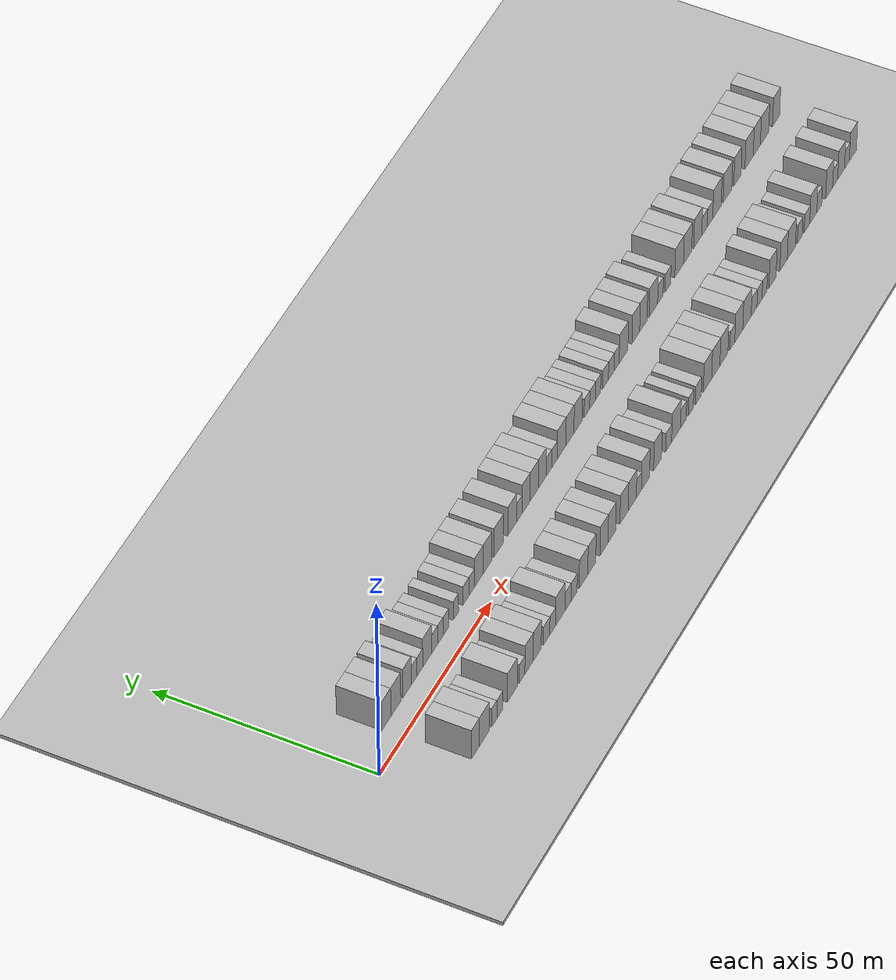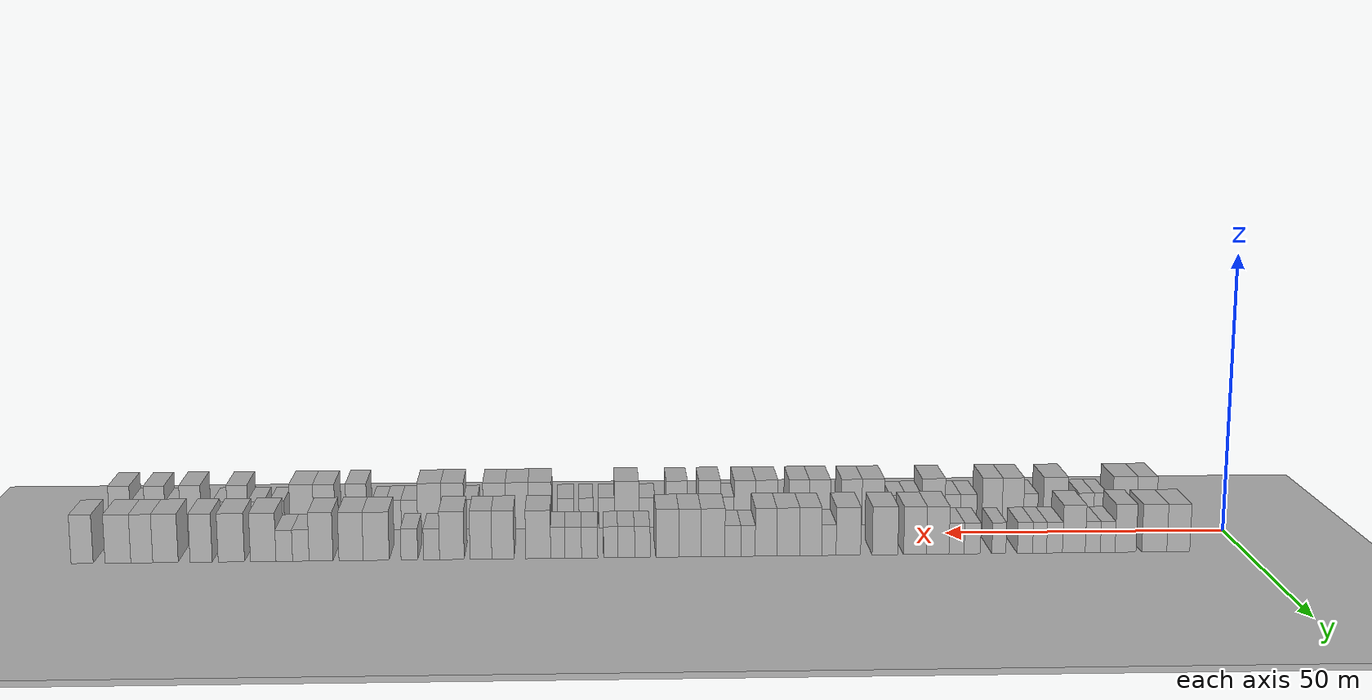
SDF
<?xml version="1.0" encoding="utf-8"?>

<sdf version="1.6">

   <world name="default">

      <gui fullscreen="0">

         <camera name="user_camera">

            <pose>-15 0 4.57585 0 0 0</pose>

            <view_controller>orbit</view_controller>

         </camera>

      </gui>

      <scene>

         <sky>

           <clouds>

             <speed>12</speed>

           </clouds>

         </sky>

         <ambient>0.4 0.4 0.4 1</ambient>

         <background>0.7 0.7 0.7 1</background>

         <shadows>1</shadows>

      </scene>

      <gravity>0 0 -9.8066</gravity>

      <magnetic_field>6e-06 2.3e-05 -4.2e-05</magnetic_field>

      <physics default="0" name="default_physics" type="ode">

         <ode>

            <solver>

               <type>quick</type>

               <iters>10</iters>

               <sor>1.0</sor>

               <use_dynamic_moi_rescaling>0</use_dynamic_moi_rescaling>

            </solver>

            <constraints>

               <cfm>0</cfm>

               <erp>0.2</erp>

               <contact_max_correcting_vel>100</contact_max_correcting_vel>

               <contact_surface_layer>0.001</contact_surface_layer>

            </constraints>

         </ode>

         <max_step_size>0.004</max_step_size>

         <real_time_factor>1</real_time_factor>

         <real_time_update_rate>250</real_time_update_rate>

      </physics>

      <light name="sun" type="directional">

         <cast_shadows>1</cast_shadows>

         <pose>0 0 10 0 0 0</pose>

         <diffuse>0.8 0.8 0.8 1</diffuse>

         <specular>0.2 0.2 0.2 1</specular>

         <attenuation>

            <range>1000</range>

            <constant>0.9</constant>

            <linear>0.01</linear>

            <quadratic>0.001</quadratic>

         </attenuation>

         <direction>-0.5 0.1 -0.9</direction>

      </light>

      <include>

         <name>ground_plane_1</name>

         <uri>model://HANNAS_ground_plane</uri>

         <pose>0 0 0  0 0 0</pose>

      </include>

      <include>

         <name>ground_plane_2</name>

         <uri>model://HANNAS_ground_plane</uri>

         <pose>100 0 0  0 0 0</pose>

      </include>

      <model name="building_1">

         <static>1</static>

         <pose frame="">12.0045 9.5000 0 0.000000 0.000000 1.570796</pose>

         <link name="link">

            <pose frame="">0 0 4.50 0 0 0</pose>

            <collision name="collision">

               <geometry>

                  <box>

                     <size>10.0000 4.0090 9.0000</size>

                  </box>

               </geometry>

               <max_contacts>10</max_contacts>

               <surface>

                  <contact>

                     <ode/>

                  </contact>

                  <bounce/>

                  <friction>

                     <torsional>

                        <ode/>

                     </torsional>

                     <ode/>

                  </friction>

               </surface>

            </collision>

            <visual name="visual">

               <cast_shadows>0</cast_shadows>

               <geometry>

                  <box>

                     <size>10.0000 4.0090 9.0000</size>

                  </box>

               </geometry>

               <material>

                  <script>

                     <uri>model://HANNAS_wall/materials/scripts</uri>

                     <uri>model://HANNAS_wall/materials/textures</uri>

                     <name>vrc/HANNAS_wall</name>

                  </script>

               </material>

            </visual>

            <self_collide>0</self_collide>

            <enable_wind>0</enable_wind>

            <kinematic>0</kinematic>

         </link>

      </model>

      <model name="building_2">

         <static>1</static>

         <pose frame="">16.1920 9.5000 0 0.000000 0.000000 1.570796</pose>

         <link name="link">

            <pose frame="">0 0 4.50 0 0 0</pose>

            <collision name="collision">

               <geometry>

                  <box>

                     <size>10.0000 4.3661 9.0000</size>

                  </box>

               </geometry>

               <max_contacts>10</max_contacts>

               <surface>

                  <contact>

                     <ode/>

                  </contact>

                  <bounce/>

                  <friction>

                     <torsional>

                        <ode/>

                     </torsional>

                     <ode/>

                  </friction>

               </surface>

            </collision>

            <visual name="visual">

               <cast_shadows>0</cast_shadows>

               <geometry>

                  <box>

                     <size>10.0000 4.3661 9.0000</size>

                  </box>

               </geometry>

               <material>

                  <script>

                     <uri>model://HANNAS_wall/materials/scripts</uri>

                     <uri>model://HANNAS_wall/materials/textures</uri>

                     <name>vrc/HANNAS_wall</name>

                  </script>

               </material>

            </visual>

            <self_collide>0</self_collide>

            <enable_wind>0</enable_wind>

            <kinematic>0</kinematic>

         </link>

      </model>

      <model name="building_3">

         <static>1</static>

         <pose frame="">21.2087 9.5000 0 0.000000 0.000000 1.570796</pose>

         <link name="link">

            <pose frame="">0 0 4.50 0 0 0</pose>

            <collision name="collision">

               <geometry>

                  <box>

                     <size>10.0000 3.6673 9.0000</size>

                  </box>

               </geometry>

               <max_contacts>10</max_contacts>

               <surface>

                  <contact>

                     <ode/>

                  </contact>

                  <bounce/>

                  <friction>

                     <torsional>

                        <ode/>

                     </torsional>

                     <ode/>

                  </friction>

               </surface>

            </collision>

            <visual name="visual">

               <cast_shadows>0</cast_shadows>

               <geometry>

                  <box>

                     <size>10.0000 3.6673 9.0000</size>

                  </box>

               </geometry>

               <material>

                  <script>

                     <uri>model://HANNAS_wall/materials/scripts</uri>

                     <uri>model://HANNAS_wall/materials/textures</uri>

                     <name>vrc/HANNAS_wall</name>

                  </script>

               </material>

            </visual>

            <self_collide>0</self_collide>

            <enable_wind>0</enable_wind>

            <kinematic>0</kinematic>

         </link>

      </model>

      <model name="building_4">

         <static>1</static>

         <pose frame="">24.3245 9.5000 0 0.000000 0.000000 1.570796</pose>

         <link name="link">

            <pose frame="">0 0 3.00 0 0 0</pose>

            <collision name="collision">

               <geometry>

                  <box>

                     <size>10.0000 2.5643 6.0000</size>

                  </box>

               </geometry>

               <max_contacts>10</max_contacts>

               <surface>

                  <contact>

                     <ode/>

                  </contact>

                  <bounce/>

                  <friction>

                     <torsional>

                        <ode/>

                     </torsional>

                     <ode/>

                  </friction>

               </surface>

            </collision>

            <visual name="visual">

               <cast_shadows>0</cast_shadows>

               <geometry>

                  <box>

                     <size>10.0000 2.5643 6.0000</size>

                  </box>

               </geometry>

               <material>

                  <script>

                     <uri>model://HANNAS_wall/materials/scripts</uri>

                     <uri>model://HANNAS_wall/materials/textures</uri>

                     <name>vrc/HANNAS_wall</name>

                  </script>

               </material>

            </visual>

            <self_collide>0</self_collide>

            <enable_wind>0</enable_wind>

            <kinematic>0</kinematic>

         </link>

      </model>

      <model name="building_5">

         <static>1</static>

         <pose frame="">26.9163 9.5000 0 0.000000 0.000000 1.570796</pose>

         <link name="link">

            <pose frame="">0 0 3.00 0 0 0</pose>

            <collision name="collision">

               <geometry>

                  <box>

                     <size>10.0000 2.6194 6.0000</size>

                  </box>

               </geometry>

               <max_contacts>10</max_contacts>

               <surface>

                  <contact>

                     <ode/>

                  </contact>

                  <bounce/>

                  <friction>

                     <torsional>

                        <ode/>

                     </torsional>

                     <ode/>

                  </friction>

               </surface>

            </collision>

            <visual name="visual">

               <cast_shadows>0</cast_shadows>

               <geometry>

                  <box>

                     <size>10.0000 2.6194 6.0000</size>

                  </box>

               </geometry>

               <material>

                  <script>

                     <uri>model://HANNAS_wall/materials/scripts</uri>

                     <uri>model://HANNAS_wall/materials/textures</uri>

                     <name>vrc/HANNAS_wall</name>

                  </script>

               </material>

            </visual>

            <self_collide>0</self_collide>

            <enable_wind>0</enable_wind>

            <kinematic>0</kinematic>

         </link>

      </model>

      <model name="building_6">

         <static>1</static>

         <pose frame="">30.2056 9.5000 0 0.000000 0.000000 1.570796</pose>

         <link name="link">

            <pose frame="">0 0 4.50 0 0 0</pose>

            <collision name="collision">

               <geometry>

                  <box>

                     <size>10.0000 3.9591 9.0000</size>

                  </box>

               </geometry>

               <max_contacts>10</max_contacts>

               <surface>

                  <contact>

                     <ode/>

                  </contact>

                  <bounce/>

                  <friction>

                     <torsional>

                        <ode/>

                     </torsional>

                     <ode/>

                  </friction>

               </surface>

            </collision>

            <visual name="visual">

               <cast_shadows>0</cast_shadows>

               <geometry>

                  <box>

                     <size>10.0000 3.9591 9.0000</size>

                  </box>

               </geometry>

               <material>

                  <script>

                     <uri>model://HANNAS_wall/materials/scripts</uri>

                     <uri>model://HANNAS_wall/materials/textures</uri>

                     <name>vrc/HANNAS_wall</name>

                  </script>

               </material>

            </visual>

            <self_collide>0</self_collide>

            <enable_wind>0</enable_wind>

            <kinematic>0</kinematic>

         </link>

      </model>

      <model name="building_7">

         <static>1</static>

         <pose frame="">33.5692 9.5000 0 0.000000 0.000000 1.570796</pose>

         <link name="link">

            <pose frame="">0 0 3.00 0 0 0</pose>

            <collision name="collision">

               <geometry>

                  <box>

                     <size>10.0000 2.7680 6.0000</size>

                  </box>

               </geometry>

               <max_contacts>10</max_contacts>

               <surface>

                  <contact>

                     <ode/>

                  </contact>

                  <bounce/>

                  <friction>

                     <torsional>

                        <ode/>

                     </torsional>

                     <ode/>

                  </friction>

               </surface>

            </collision>

            <visual name="visual">

               <cast_shadows>0</cast_shadows>

               <geometry>

                  <box>

                     <size>10.0000 2.7680 6.0000</size>

                  </box>

               </geometry>

               <material>

                  <script>

                     <uri>model://HANNAS_wall/materials/scripts</uri>

                     <uri>model://HANNAS_wall/materials/textures</uri>

                     <name>vrc/HANNAS_wall</name>

                  </script>

               </material>

            </visual>

            <self_collide>0</self_collide>

            <enable_wind>0</enable_wind>

            <kinematic>0</kinematic>

         </link>

      </model>

      <model name="building_8">

         <static>1</static>

         <pose frame="">36.1631 9.5000 0 0.000000 0.000000 1.570796</pose>

         <link name="link">

            <pose frame="">0 0 3.00 0 0 0</pose>

            <collision name="collision">

               <geometry>

                  <box>

                     <size>10.0000 2.4198 6.0000</size>

                  </box>

               </geometry>

               <max_contacts>10</max_contacts>

               <surface>

                  <contact>

                     <ode/>

                  </contact>

                  <bounce/>

                  <friction>

                     <torsional>

                        <ode/>

                     </torsional>

                     <ode/>

                  </friction>

               </surface>

            </collision>

            <visual name="visual">

               <cast_shadows>0</cast_shadows>

               <geometry>

                  <box>

                     <size>10.0000 2.4198 6.0000</size>

                  </box>

               </geometry>

               <material>

                  <script>

                     <uri>model://HANNAS_wall/materials/scripts</uri>

                     <uri>model://HANNAS_wall/materials/textures</uri>

                     <name>vrc/HANNAS_wall</name>

                  </script>

               </material>

            </visual>

            <self_collide>0</self_collide>

            <enable_wind>0</enable_wind>

            <kinematic>0</kinematic>

         </link>

      </model>

      <model name="building_9">

         <static>1</static>

         <pose frame="">38.6890 9.5000 0 0.000000 0.000000 1.570796</pose>

         <link name="link">

            <pose frame="">0 0 3.00 0 0 0</pose>

            <collision name="collision">

               <geometry>

                  <box>

                     <size>10.0000 2.6320 6.0000</size>

                  </box>

               </geometry>

               <max_contacts>10</max_contacts>

               <surface>

                  <contact>

                     <ode/>

                  </contact>

                  <bounce/>

                  <friction>

                     <torsional>

                        <ode/>

                     </torsional>

                     <ode/>

                  </friction>

               </surface>

            </collision>

            <visual name="visual">

               <cast_shadows>0</cast_shadows>

               <geometry>

                  <box>

                     <size>10.0000 2.6320 6.0000</size>

                  </box>

               </geometry>

               <material>

                  <script>

                     <uri>model://HANNAS_wall/materials/scripts</uri>

                     <uri>model://HANNAS_wall/materials/textures</uri>

                     <name>vrc/HANNAS_wall</name>

                  </script>

               </material>

            </visual>

            <self_collide>0</self_collide>

            <enable_wind>0</enable_wind>

            <kinematic>0</kinematic>

         </link>

      </model>

      <model name="building_10">

         <static>1</static>

         <pose frame="">43.2170 9.5000 0 0.000000 0.000000 1.570796</pose>

         <link name="link">

            <pose frame="">0 0 3.00 0 0 0</pose>

            <collision name="collision">

               <geometry>

                  <box>

                     <size>10.0000 2.4241 6.0000</size>

                  </box>

               </geometry>

               <max_contacts>10</max_contacts>

               <surface>

                  <contact>

                     <ode/>

                  </contact>

                  <bounce/>

                  <friction>

                     <torsional>

                        <ode/>

                     </torsional>

                     <ode/>

                  </friction>

               </surface>

            </collision>

            <visual name="visual">

               <cast_shadows>0</cast_shadows>

               <geometry>

                  <box>

                     <size>10.0000 2.4241 6.0000</size>

                  </box>

               </geometry>

               <material>

                  <script>

                     <uri>model://HANNAS_wall/materials/scripts</uri>

                     <uri>model://HANNAS_wall/materials/textures</uri>

                     <name>vrc/HANNAS_wall</name>

                  </script>

               </material>

            </visual>

            <self_collide>0</self_collide>

            <enable_wind>0</enable_wind>

            <kinematic>0</kinematic>

         </link>

      </model>

      <model name="building_11">

         <static>1</static>

         <pose frame="">47.8303 9.5000 0 0.000000 0.000000 1.570796</pose>

         <link name="link">

            <pose frame="">0 0 3.00 0 0 0</pose>

            <collision name="collision">

               <geometry>

                  <box>

                     <size>10.0000 2.8025 6.0000</size>

                  </box>

               </geometry>

               <max_contacts>10</max_contacts>

               <surface>

                  <contact>

                     <ode/>

                  </contact>

                  <bounce/>

                  <friction>

                     <torsional>

                        <ode/>

                     </torsional>

                     <ode/>

                  </friction>

               </surface>

            </collision>

            <visual name="visual">

               <cast_shadows>0</cast_shadows>

               <geometry>

                  <box>

                     <size>10.0000 2.8025 6.0000</size>

                  </box>

               </geometry>

               <material>

                  <script>

                     <uri>model://HANNAS_wall/materials/scripts</uri>

                     <uri>model://HANNAS_wall/materials/textures</uri>

                     <name>vrc/HANNAS_wall</name>

                  </script>

               </material>

            </visual>

            <self_collide>0</self_collide>

            <enable_wind>0</enable_wind>

            <kinematic>0</kinematic>

         </link>

      </model>

      <model name="building_12">

         <static>1</static>

         <pose frame="">50.5448 9.5000 0 0.000000 0.000000 1.570796</pose>

         <link name="link">

            <pose frame="">0 0 3.00 0 0 0</pose>

            <collision name="collision">

               <geometry>

                  <box>

                     <size>10.0000 2.6265 6.0000</size>

                  </box>

               </geometry>

               <max_contacts>10</max_contacts>

               <surface>

                  <contact>

                     <ode/>

                  </contact>

                  <bounce/>

                  <friction>

                     <torsional>

                        <ode/>

                     </torsional>

                     <ode/>

                  </friction>

               </surface>

            </collision>

            <visual name="visual">

               <cast_shadows>0</cast_shadows>

               <geometry>

                  <box>

                     <size>10.0000 2.6265 6.0000</size>

                  </box>

               </geometry>

               <material>

                  <script>

                     <uri>model://HANNAS_wall/materials/scripts</uri>

                     <uri>model://HANNAS_wall/materials/textures</uri>

                     <name>vrc/HANNAS_wall</name>

                  </script>

               </material>

            </visual>

            <self_collide>0</self_collide>

            <enable_wind>0</enable_wind>

            <kinematic>0</kinematic>

         </link>

      </model>

      <model name="building_13">

         <static>1</static>

         <pose frame="">53.8044 9.5000 0 0.000000 0.000000 1.570796</pose>

         <link name="link">

            <pose frame="">0 0 4.50 0 0 0</pose>

            <collision name="collision">

               <geometry>

                  <box>

                     <size>10.0000 3.8926 9.0000</size>

                  </box>

               </geometry>

               <max_contacts>10</max_contacts>

               <surface>

                  <contact>

                     <ode/>

                  </contact>

                  <bounce/>

                  <friction>

                     <torsional>

                        <ode/>

                     </torsional>

                     <ode/>

                  </friction>

               </surface>

            </collision>

            <visual name="visual">

               <cast_shadows>0</cast_shadows>

               <geometry>

                  <box>

                     <size>10.0000 3.8926 9.0000</size>

                  </box>

               </geometry>

               <material>

                  <script>

                     <uri>model://HANNAS_wall/materials/scripts</uri>

                     <uri>model://HANNAS_wall/materials/textures</uri>

                     <name>vrc/HANNAS_wall</name>

                  </script>

               </material>

            </visual>

            <self_collide>0</self_collide>

            <enable_wind>0</enable_wind>

            <kinematic>0</kinematic>

         </link>

      </model>

      <model name="building_14">

         <static>1</static>

         <pose frame="">57.7253 9.5000 0 0.000000 0.000000 1.570796</pose>

         <link name="link">

            <pose frame="">0 0 4.50 0 0 0</pose>

            <collision name="collision">

               <geometry>

                  <box>

                     <size>10.0000 3.9492 9.0000</size>

                  </box>

               </geometry>

               <max_contacts>10</max_contacts>

               <surface>

                  <contact>

                     <ode/>

                  </contact>

                  <bounce/>

                  <friction>

                     <torsional>

                        <ode/>

                     </torsional>

                     <ode/>

                  </friction>

               </surface>

            </collision>

            <visual name="visual">

               <cast_shadows>0</cast_shadows>

               <geometry>

                  <box>

                     <size>10.0000 3.9492 9.0000</size>

                  </box>

               </geometry>

               <material>

                  <script>

                     <uri>model://HANNAS_wall/materials/scripts</uri>

                     <uri>model://HANNAS_wall/materials/textures</uri>

                     <name>vrc/HANNAS_wall</name>

                  </script>

               </material>

            </visual>

            <self_collide>0</self_collide>

            <enable_wind>0</enable_wind>

            <kinematic>0</kinematic>

         </link>

      </model>

      <model name="building_15">

         <static>1</static>

         <pose frame="">62.9188 9.5000 0 0.000000 0.000000 1.570796</pose>

         <link name="link">

            <pose frame="">0 0 4.50 0 0 0</pose>

            <collision name="collision">

               <geometry>

                  <box>

                     <size>10.0000 4.4379 9.0000</size>

                  </box>

               </geometry>

               <max_contacts>10</max_contacts>

               <surface>

                  <contact>

                     <ode/>

                  </contact>

                  <bounce/>

                  <friction>

                     <torsional>

                        <ode/>

                     </torsional>

                     <ode/>

                  </friction>

               </surface>

            </collision>

            <visual name="visual">

               <cast_shadows>0</cast_shadows>

               <geometry>

                  <box>

                     <size>10.0000 4.4379 9.0000</size>

                  </box>

               </geometry>

               <material>

                  <script>

                     <uri>model://HANNAS_wall/materials/scripts</uri>

                     <uri>model://HANNAS_wall/materials/textures</uri>

                     <name>vrc/HANNAS_wall</name>

                  </script>

               </material>

            </visual>

            <self_collide>0</self_collide>

            <enable_wind>0</enable_wind>

            <kinematic>0</kinematic>

         </link>

      </model>

      <model name="building_16">

         <static>1</static>

         <pose frame="">69.2543 9.5000 0 0.000000 0.000000 1.570796</pose>

         <link name="link">

            <pose frame="">0 0 4.50 0 0 0</pose>

            <collision name="collision">

               <geometry>

                  <box>

                     <size>10.0000 4.2331 9.0000</size>

                  </box>

               </geometry>

               <max_contacts>10</max_contacts>

               <surface>

                  <contact>

                     <ode/>

                  </contact>

                  <bounce/>

                  <friction>

                     <torsional>

                        <ode/>

                     </torsional>

                     <ode/>

                  </friction>

               </surface>

            </collision>

            <visual name="visual">

               <cast_shadows>0</cast_shadows>

               <geometry>

                  <box>

                     <size>10.0000 4.2331 9.0000</size>

                  </box>

               </geometry>

               <material>

                  <script>

                     <uri>model://HANNAS_wall/materials/scripts</uri>

                     <uri>model://HANNAS_wall/materials/textures</uri>

                     <name>vrc/HANNAS_wall</name>

                  </script>

               </material>

            </visual>

            <self_collide>0</self_collide>

            <enable_wind>0</enable_wind>

            <kinematic>0</kinematic>

         </link>

      </model>

      <model name="building_17">

         <static>1</static>

         <pose frame="">72.6155 9.5000 0 0.000000 0.000000 1.570796</pose>

         <link name="link">

            <pose frame="">0 0 3.00 0 0 0</pose>

            <collision name="collision">

               <geometry>

                  <box>

                     <size>10.0000 2.4891 6.0000</size>

                  </box>

               </geometry>

               <max_contacts>10</max_contacts>

               <surface>

                  <contact>

                     <ode/>

                  </contact>

                  <bounce/>

                  <friction>

                     <torsional>

                        <ode/>

                     </torsional>

                     <ode/>

                  </friction>

               </surface>

            </collision>

            <visual name="visual">

               <cast_shadows>0</cast_shadows>

               <geometry>

                  <box>

                     <size>10.0000 2.4891 6.0000</size>

                  </box>

               </geometry>

               <material>

                  <script>

                     <uri>model://HANNAS_wall/materials/scripts</uri>

                     <uri>model://HANNAS_wall/materials/textures</uri>

                     <name>vrc/HANNAS_wall</name>

                  </script>

               </material>

            </visual>

            <self_collide>0</self_collide>

            <enable_wind>0</enable_wind>

            <kinematic>0</kinematic>

         </link>

      </model>

      <model name="building_18">

         <static>1</static>

         <pose frame="">75.7572 9.5000 0 0.000000 0.000000 1.570796</pose>

         <link name="link">

            <pose frame="">0 0 4.50 0 0 0</pose>

            <collision name="collision">

               <geometry>

                  <box>

                     <size>10.0000 3.7943 9.0000</size>

                  </box>

               </geometry>

               <max_contacts>10</max_contacts>

               <surface>

                  <contact>

                     <ode/>

                  </contact>

                  <bounce/>

                  <friction>

                     <torsional>

                        <ode/>

                     </torsional>

                     <ode/>

                  </friction>

               </surface>

            </collision>

            <visual name="visual">

               <cast_shadows>0</cast_shadows>

               <geometry>

                  <box>

                     <size>10.0000 3.7943 9.0000</size>

                  </box>

               </geometry>

               <material>

                  <script>

                     <uri>model://HANNAS_wall/materials/scripts</uri>

                     <uri>model://HANNAS_wall/materials/textures</uri>

                     <name>vrc/HANNAS_wall</name>

                  </script>

               </material>

            </visual>

            <self_collide>0</self_collide>

            <enable_wind>0</enable_wind>

            <kinematic>0</kinematic>

         </link>

      </model>

      <model name="building_19">

         <static>1</static>

         <pose frame="">79.6302 9.5000 0 0.000000 0.000000 1.570796</pose>

         <link name="link">

            <pose frame="">0 0 4.50 0 0 0</pose>

            <collision name="collision">

               <geometry>

                  <box>

                     <size>10.0000 3.9518 9.0000</size>

                  </box>

               </geometry>

               <max_contacts>10</max_contacts>

               <surface>

                  <contact>

                     <ode/>

                  </contact>

                  <bounce/>

                  <friction>

                     <torsional>

                        <ode/>

                     </torsional>

                     <ode/>

                  </friction>

               </surface>

            </collision>

            <visual name="visual">

               <cast_shadows>0</cast_shadows>

               <geometry>

                  <box>

                     <size>10.0000 3.9518 9.0000</size>

                  </box>

               </geometry>

               <material>

                  <script>

                     <uri>model://HANNAS_wall/materials/scripts</uri>

                     <uri>model://HANNAS_wall/materials/textures</uri>

                     <name>vrc/HANNAS_wall</name>

                  </script>

               </material>

            </visual>

            <self_collide>0</self_collide>

            <enable_wind>0</enable_wind>

            <kinematic>0</kinematic>

         </link>

      </model>

      <model name="building_20">

         <static>1</static>

         <pose frame="">83.4527 9.5000 0 0.000000 0.000000 1.570796</pose>

         <link name="link">

            <pose frame="">0 0 4.50 0 0 0</pose>

            <collision name="collision">

               <geometry>

                  <box>

                     <size>10.0000 3.6931 9.0000</size>

                  </box>

               </geometry>

               <max_contacts>10</max_contacts>

               <surface>

                  <contact>

                     <ode/>

                  </contact>

                  <bounce/>

                  <friction>

                     <torsional>

                        <ode/>

                     </torsional>

                     <ode/>

                  </friction>

               </surface>

            </collision>

            <visual name="visual">

               <cast_shadows>0</cast_shadows>

               <geometry>

                  <box>

                     <size>10.0000 3.6931 9.0000</size>

                  </box>

               </geometry>

               <material>

                  <script>

                     <uri>model://HANNAS_wall/materials/scripts</uri>

                     <uri>model://HANNAS_wall/materials/textures</uri>

                     <name>vrc/HANNAS_wall</name>

                  </script>

               </material>

            </visual>

            <self_collide>0</self_collide>

            <enable_wind>0</enable_wind>

            <kinematic>0</kinematic>

         </link>

      </model>

      <model name="building_21">

         <static>1</static>

         <pose frame="">86.5423 9.5000 0 0.000000 0.000000 1.570796</pose>

         <link name="link">

            <pose frame="">0 0 3.00 0 0 0</pose>

            <collision name="collision">

               <geometry>

                  <box>

                     <size>10.0000 2.4860 6.0000</size>

                  </box>

               </geometry>

               <max_contacts>10</max_contacts>

               <surface>

                  <contact>

                     <ode/>

                  </contact>

                  <bounce/>

                  <friction>

                     <torsional>

                        <ode/>

                     </torsional>

                     <ode/>

                  </friction>

               </surface>

            </collision>

            <visual name="visual">

               <cast_shadows>0</cast_shadows>

               <geometry>

                  <box>

                     <size>10.0000 2.4860 6.0000</size>

                  </box>

               </geometry>

               <material>

                  <script>

                     <uri>model://HANNAS_wall/materials/scripts</uri>

                     <uri>model://HANNAS_wall/materials/textures</uri>

                     <name>vrc/HANNAS_wall</name>

                  </script>

               </material>

            </visual>

            <self_collide>0</self_collide>

            <enable_wind>0</enable_wind>

            <kinematic>0</kinematic>

         </link>

      </model>

      <model name="building_22">

         <static>1</static>

         <pose frame="">89.1378 9.5000 0 0.000000 0.000000 1.570796</pose>

         <link name="link">

            <pose frame="">0 0 3.00 0 0 0</pose>

            <collision name="collision">

               <geometry>

                  <box>

                     <size>10.0000 2.7049 6.0000</size>

                  </box>

               </geometry>

               <max_contacts>10</max_contacts>

               <surface>

                  <contact>

                     <ode/>

                  </contact>

                  <bounce/>

                  <friction>

                     <torsional>

                        <ode/>

                     </torsional>

                     <ode/>

                  </friction>

               </surface>

            </collision>

            <visual name="visual">

               <cast_shadows>0</cast_shadows>

               <geometry>

                  <box>

                     <size>10.0000 2.7049 6.0000</size>

                  </box>

               </geometry>

               <material>

                  <script>

                     <uri>model://HANNAS_wall/materials/scripts</uri>

                     <uri>model://HANNAS_wall/materials/textures</uri>

                     <name>vrc/HANNAS_wall</name>

                  </script>

               </material>

            </visual>

            <self_collide>0</self_collide>

            <enable_wind>0</enable_wind>

            <kinematic>0</kinematic>

         </link>

      </model>

      <model name="building_23">

         <static>1</static>

         <pose frame="">92.5736 9.5000 0 0.000000 0.000000 1.570796</pose>

         <link name="link">

            <pose frame="">0 0 4.50 0 0 0</pose>

            <collision name="collision">

               <geometry>

                  <box>

                     <size>10.0000 4.1667 9.0000</size>

                  </box>

               </geometry>

               <max_contacts>10</max_contacts>

               <surface>

                  <contact>

                     <ode/>

                  </contact>

                  <bounce/>

                  <friction>

                     <torsional>

                        <ode/>

                     </torsional>

                     <ode/>

                  </friction>

               </surface>

            </collision>

            <visual name="visual">

               <cast_shadows>0</cast_shadows>

               <geometry>

                  <box>

                     <size>10.0000 4.1667 9.0000</size>

                  </box>

               </geometry>

               <material>

                  <script>

                     <uri>model://HANNAS_wall/materials/scripts</uri>

                     <uri>model://HANNAS_wall/materials/textures</uri>

                     <name>vrc/HANNAS_wall</name>

                  </script>

               </material>

            </visual>

            <self_collide>0</self_collide>

            <enable_wind>0</enable_wind>

            <kinematic>0</kinematic>

         </link>

      </model>

      <model name="building_24">

         <static>1</static>

         <pose frame="">96.5496 9.5000 0 0.000000 0.000000 1.570796</pose>

         <link name="link">

            <pose frame="">0 0 4.50 0 0 0</pose>

            <collision name="collision">

               <geometry>

                  <box>

                     <size>10.0000 3.7852 9.0000</size>

                  </box>

               </geometry>

               <max_contacts>10</max_contacts>

               <surface>

                  <contact>

                     <ode/>

                  </contact>

                  <bounce/>

                  <friction>

                     <torsional>

                        <ode/>

                     </torsional>

                     <ode/>

                  </friction>

               </surface>

            </collision>

            <visual name="visual">

               <cast_shadows>0</cast_shadows>

               <geometry>

                  <box>

                     <size>10.0000 3.7852 9.0000</size>

                  </box>

               </geometry>

               <material>

                  <script>

                     <uri>model://HANNAS_wall/materials/scripts</uri>

                     <uri>model://HANNAS_wall/materials/textures</uri>

                     <name>vrc/HANNAS_wall</name>

                  </script>

               </material>

            </visual>

            <self_collide>0</self_collide>

            <enable_wind>0</enable_wind>

            <kinematic>0</kinematic>

         </link>

      </model>

      <model name="building_25">

         <static>1</static>

         <pose frame="">100.3925 9.5000 0 0.000000 0.000000 1.570796</pose>

         <link name="link">

            <pose frame="">0 0 4.50 0 0 0</pose>

            <collision name="collision">

               <geometry>

                  <box>

                     <size>10.0000 3.9007 9.0000</size>

                  </box>

               </geometry>

               <max_contacts>10</max_contacts>

               <surface>

                  <contact>

                     <ode/>

                  </contact>

                  <bounce/>

                  <friction>

                     <torsional>

                        <ode/>

                     </torsional>

                     <ode/>

                  </friction>

               </surface>

            </collision>

            <visual name="visual">

               <cast_shadows>0</cast_shadows>

               <geometry>

                  <box>

                     <size>10.0000 3.9007 9.0000</size>

                  </box>

               </geometry>

               <material>

                  <script>

                     <uri>model://HANNAS_wall/materials/scripts</uri>

                     <uri>model://HANNAS_wall/materials/textures</uri>

                     <name>vrc/HANNAS_wall</name>

                  </script>

               </material>

            </visual>

            <self_collide>0</self_collide>

            <enable_wind>0</enable_wind>

            <kinematic>0</kinematic>

         </link>

      </model>

      <model name="building_26">

         <static>1</static>

         <pose frame="">104.6687 9.5000 0 0.000000 0.000000 1.570796</pose>

         <link name="link">

            <pose frame="">0 0 3.00 0 0 0</pose>

            <collision name="collision">

               <geometry>

                  <box>

                     <size>10.0000 2.6517 6.0000</size>

                  </box>

               </geometry>

               <max_contacts>10</max_contacts>

               <surface>

                  <contact>

                     <ode/>

                  </contact>

                  <bounce/>

                  <friction>

                     <torsional>

                        <ode/>

                     </torsional>

                     <ode/>

                  </friction>

               </surface>

            </collision>

            <visual name="visual">

               <cast_shadows>0</cast_shadows>

               <geometry>

                  <box>

                     <size>10.0000 2.6517 6.0000</size>

                  </box>

               </geometry>

               <material>

                  <script>

                     <uri>model://HANNAS_wall/materials/scripts</uri>

                     <uri>model://HANNAS_wall/materials/textures</uri>

                     <name>vrc/HANNAS_wall</name>

                  </script>

               </material>

            </visual>

            <self_collide>0</self_collide>

            <enable_wind>0</enable_wind>

            <kinematic>0</kinematic>

         </link>

      </model>

      <model name="building_27">

         <static>1</static>

         <pose frame="">107.4407 9.5000 0 0.000000 0.000000 1.570796</pose>

         <link name="link">

            <pose frame="">0 0 3.00 0 0 0</pose>

            <collision name="collision">

               <geometry>

                  <box>

                     <size>10.0000 2.8923 6.0000</size>

                  </box>

               </geometry>

               <max_contacts>10</max_contacts>

               <surface>

                  <contact>

                     <ode/>

                  </contact>

                  <bounce/>

                  <friction>

                     <torsional>

                        <ode/>

                     </torsional>

                     <ode/>

                  </friction>

               </surface>

            </collision>

            <visual name="visual">

               <cast_shadows>0</cast_shadows>

               <geometry>

                  <box>

                     <size>10.0000 2.8923 6.0000</size>

                  </box>

               </geometry>

               <material>

                  <script>

                     <uri>model://HANNAS_wall/materials/scripts</uri>

                     <uri>model://HANNAS_wall/materials/textures</uri>

                     <name>vrc/HANNAS_wall</name>

                  </script>

               </material>

            </visual>

            <self_collide>0</self_collide>

            <enable_wind>0</enable_wind>

            <kinematic>0</kinematic>

         </link>

      </model>

      <model name="building_28">

         <static>1</static>

         <pose frame="">110.0935 9.5000 0 0.000000 0.000000 1.570796</pose>

         <link name="link">

            <pose frame="">0 0 3.00 0 0 0</pose>

            <collision name="collision">

               <geometry>

                  <box>

                     <size>10.0000 2.4133 6.0000</size>

                  </box>

               </geometry>

               <max_contacts>10</max_contacts>

               <surface>

                  <contact>

                     <ode/>

                  </contact>

                  <bounce/>

                  <friction>

                     <torsional>

                        <ode/>

                     </torsional>

                     <ode/>

                  </friction>

               </surface>

            </collision>

            <visual name="visual">

               <cast_shadows>0</cast_shadows>

               <geometry>

                  <box>

                     <size>10.0000 2.4133 6.0000</size>

                  </box>

               </geometry>

               <material>

                  <script>

                     <uri>model://HANNAS_wall/materials/scripts</uri>

                     <uri>model://HANNAS_wall/materials/textures</uri>

                     <name>vrc/HANNAS_wall</name>

                  </script>

               </material>

            </visual>

            <self_collide>0</self_collide>

            <enable_wind>0</enable_wind>

            <kinematic>0</kinematic>

         </link>

      </model>

      <model name="building_29">

         <static>1</static>

         <pose frame="">113.6905 9.5000 0 0.000000 0.000000 1.570796</pose>

         <link name="link">

            <pose frame="">0 0 3.00 0 0 0</pose>

            <collision name="collision">

               <geometry>

                  <box>

                     <size>10.0000 2.7808 6.0000</size>

                  </box>

               </geometry>

               <max_contacts>10</max_contacts>

               <surface>

                  <contact>

                     <ode/>

                  </contact>

                  <bounce/>

                  <friction>

                     <torsional>

                        <ode/>

                     </torsional>

                     <ode/>

                  </friction>

               </surface>

            </collision>

            <visual name="visual">

               <cast_shadows>0</cast_shadows>

               <geometry>

                  <box>

                     <size>10.0000 2.7808 6.0000</size>

                  </box>

               </geometry>

               <material>

                  <script>

                     <uri>model://HANNAS_wall/materials/scripts</uri>

                     <uri>model://HANNAS_wall/materials/textures</uri>

                     <name>vrc/HANNAS_wall</name>

                  </script>

               </material>

            </visual>

            <self_collide>0</self_collide>

            <enable_wind>0</enable_wind>

            <kinematic>0</kinematic>

         </link>

      </model>

      <model name="building_30">

         <static>1</static>

         <pose frame="">116.5010 9.5000 0 0.000000 0.000000 1.570796</pose>

         <link name="link">

            <pose frame="">0 0 3.00 0 0 0</pose>

            <collision name="collision">

               <geometry>

                  <box>

                     <size>10.0000 2.8401 6.0000</size>

                  </box>

               </geometry>

               <max_contacts>10</max_contacts>

               <surface>

                  <contact>

                     <ode/>

                  </contact>

                  <bounce/>

                  <friction>

                     <torsional>

                        <ode/>

                     </torsional>

                     <ode/>

                  </friction>

               </surface>

            </collision>

            <visual name="visual">

               <cast_shadows>0</cast_shadows>

               <geometry>

                  <box>

                     <size>10.0000 2.8401 6.0000</size>

                  </box>

               </geometry>

               <material>

                  <script>

                     <uri>model://HANNAS_wall/materials/scripts</uri>

                     <uri>model://HANNAS_wall/materials/textures</uri>

                     <name>vrc/HANNAS_wall</name>

                  </script>

               </material>

            </visual>

            <self_collide>0</self_collide>

            <enable_wind>0</enable_wind>

            <kinematic>0</kinematic>

         </link>

      </model>

      <model name="building_31">

         <static>1</static>

         <pose frame="">119.1391 9.5000 0 0.000000 0.000000 1.570796</pose>

         <link name="link">

            <pose frame="">0 0 3.00 0 0 0</pose>

            <collision name="collision">

               <geometry>

                  <box>

                     <size>10.0000 2.4362 6.0000</size>

                  </box>

               </geometry>

               <max_contacts>10</max_contacts>

               <surface>

                  <contact>

                     <ode/>

                  </contact>

                  <bounce/>

                  <friction>

                     <torsional>

                        <ode/>

                     </torsional>

                     <ode/>

                  </friction>

               </surface>

            </collision>

            <visual name="visual">

               <cast_shadows>0</cast_shadows>

               <geometry>

                  <box>

                     <size>10.0000 2.4362 6.0000</size>

                  </box>

               </geometry>

               <material>

                  <script>

                     <uri>model://HANNAS_wall/materials/scripts</uri>

                     <uri>model://HANNAS_wall/materials/textures</uri>

                     <name>vrc/HANNAS_wall</name>

                  </script>

               </material>

            </visual>

            <self_collide>0</self_collide>

            <enable_wind>0</enable_wind>

            <kinematic>0</kinematic>

         </link>

      </model>

      <model name="building_32">

         <static>1</static>

         <pose frame="">122.4909 9.5000 0 0.000000 0.000000 1.570796</pose>

         <link name="link">

            <pose frame="">0 0 4.50 0 0 0</pose>

            <collision name="collision">

               <geometry>

                  <box>

                     <size>10.0000 4.2673 9.0000</size>

                  </box>

               </geometry>

               <max_contacts>10</max_contacts>

               <surface>

                  <contact>

                     <ode/>

                  </contact>

                  <bounce/>

                  <friction>

                     <torsional>

                        <ode/>

                     </torsional>

                     <ode/>

                  </friction>

               </surface>

            </collision>

            <visual name="visual">

               <cast_shadows>0</cast_shadows>

               <geometry>

                  <box>

                     <size>10.0000 4.2673 9.0000</size>

                  </box>

               </geometry>

               <material>

                  <script>

                     <uri>model://HANNAS_wall/materials/scripts</uri>

                     <uri>model://HANNAS_wall/materials/textures</uri>

                     <name>vrc/HANNAS_wall</name>

                  </script>

               </material>

            </visual>

            <self_collide>0</self_collide>

            <enable_wind>0</enable_wind>

            <kinematic>0</kinematic>

         </link>

      </model>

      <model name="building_33">

         <static>1</static>

         <pose frame="">128.5129 9.5000 0 0.000000 0.000000 1.570796</pose>

         <link name="link">

            <pose frame="">0 0 4.50 0 0 0</pose>

            <collision name="collision">

               <geometry>

                  <box>

                     <size>10.0000 3.7769 9.0000</size>

                  </box>

               </geometry>

               <max_contacts>10</max_contacts>

               <surface>

                  <contact>

                     <ode/>

                  </contact>

                  <bounce/>

                  <friction>

                     <torsional>

                        <ode/>

                     </torsional>

                     <ode/>

                  </friction>

               </surface>

            </collision>

            <visual name="visual">

               <cast_shadows>0</cast_shadows>

               <geometry>

                  <box>

                     <size>10.0000 3.7769 9.0000</size>

                  </box>

               </geometry>

               <material>

                  <script>

                     <uri>model://HANNAS_wall/materials/scripts</uri>

                     <uri>model://HANNAS_wall/materials/textures</uri>

                     <name>vrc/HANNAS_wall</name>

                  </script>

               </material>

            </visual>

            <self_collide>0</self_collide>

            <enable_wind>0</enable_wind>

            <kinematic>0</kinematic>

         </link>

      </model>

      <model name="building_34">

         <static>1</static>

         <pose frame="">132.2563 9.5000 0 0.000000 0.000000 1.570796</pose>

         <link name="link">

            <pose frame="">0 0 4.50 0 0 0</pose>

            <collision name="collision">

               <geometry>

                  <box>

                     <size>10.0000 3.7100 9.0000</size>

                  </box>

               </geometry>

               <max_contacts>10</max_contacts>

               <surface>

                  <contact>

                     <ode/>

                  </contact>

                  <bounce/>

                  <friction>

                     <torsional>

                        <ode/>

                     </torsional>

                     <ode/>

                  </friction>

               </surface>

            </collision>

            <visual name="visual">

               <cast_shadows>0</cast_shadows>

               <geometry>

                  <box>

                     <size>10.0000 3.7100 9.0000</size>

                  </box>

               </geometry>

               <material>

                  <script>

                     <uri>model://HANNAS_wall/materials/scripts</uri>

                     <uri>model://HANNAS_wall/materials/textures</uri>

                     <name>vrc/HANNAS_wall</name>

                  </script>

               </material>

            </visual>

            <self_collide>0</self_collide>

            <enable_wind>0</enable_wind>

            <kinematic>0</kinematic>

         </link>

      </model>

      <model name="building_35">

         <static>1</static>

         <pose frame="">137.2074 9.5000 0 0.000000 0.000000 1.570796</pose>

         <link name="link">

            <pose frame="">0 0 4.50 0 0 0</pose>

            <collision name="collision">

               <geometry>

                  <box>

                     <size>10.0000 4.1921 9.0000</size>

                  </box>

               </geometry>

               <max_contacts>10</max_contacts>

               <surface>

                  <contact>

                     <ode/>

                  </contact>

                  <bounce/>

                  <friction>

                     <torsional>

                        <ode/>

                     </torsional>

                     <ode/>

                  </friction>

               </surface>

            </collision>

            <visual name="visual">

               <cast_shadows>0</cast_shadows>

               <geometry>

                  <box>

                     <size>10.0000 4.1921 9.0000</size>

                  </box>

               </geometry>

               <material>

                  <script>

                     <uri>model://HANNAS_wall/materials/scripts</uri>

                     <uri>model://HANNAS_wall/materials/textures</uri>

                     <name>vrc/HANNAS_wall</name>

                  </script>

               </material>

            </visual>

            <self_collide>0</self_collide>

            <enable_wind>0</enable_wind>

            <kinematic>0</kinematic>

         </link>

      </model>

      <model name="building_36">

         <static>1</static>

         <pose frame="">140.6549 9.5000 0 0.000000 0.000000 1.570796</pose>

         <link name="link">

            <pose frame="">0 0 3.00 0 0 0</pose>

            <collision name="collision">

               <geometry>

                  <box>

                     <size>10.0000 2.7029 6.0000</size>

                  </box>

               </geometry>

               <max_contacts>10</max_contacts>

               <surface>

                  <contact>

                     <ode/>

                  </contact>

                  <bounce/>

                  <friction>

                     <torsional>

                        <ode/>

                     </torsional>

                     <ode/>

                  </friction>

               </surface>

            </collision>

            <visual name="visual">

               <cast_shadows>0</cast_shadows>

               <geometry>

                  <box>

                     <size>10.0000 2.7029 6.0000</size>

                  </box>

               </geometry>

               <material>

                  <script>

                     <uri>model://HANNAS_wall/materials/scripts</uri>

                     <uri>model://HANNAS_wall/materials/textures</uri>

                     <name>vrc/HANNAS_wall</name>

                  </script>

               </material>

            </visual>

            <self_collide>0</self_collide>

            <enable_wind>0</enable_wind>

            <kinematic>0</kinematic>

         </link>

      </model>

      <model name="building_37">

         <static>1</static>

         <pose frame="">144.4302 9.5000 0 0.000000 0.000000 1.570796</pose>

         <link name="link">

            <pose frame="">0 0 3.00 0 0 0</pose>

            <collision name="collision">

               <geometry>

                  <box>

                     <size>10.0000 2.8476 6.0000</size>

                  </box>

               </geometry>

               <max_contacts>10</max_contacts>

               <surface>

                  <contact>

                     <ode/>

                  </contact>

                  <bounce/>

                  <friction>

                     <torsional>

                        <ode/>

                     </torsional>

                     <ode/>

                  </friction>

               </surface>

            </collision>

            <visual name="visual">

               <cast_shadows>0</cast_shadows>

               <geometry>

                  <box>

                     <size>10.0000 2.8476 6.0000</size>

                  </box>

               </geometry>

               <material>

                  <script>

                     <uri>model://HANNAS_wall/materials/scripts</uri>

                     <uri>model://HANNAS_wall/materials/textures</uri>

                     <name>vrc/HANNAS_wall</name>

                  </script>

               </material>

            </visual>

            <self_collide>0</self_collide>

            <enable_wind>0</enable_wind>

            <kinematic>0</kinematic>

         </link>

      </model>

      <model name="building_38">

         <static>1</static>

         <pose frame="">150.0577 9.5000 0 0.000000 0.000000 1.570796</pose>

         <link name="link">

            <pose frame="">0 0 4.50 0 0 0</pose>

            <collision name="collision">

               <geometry>

                  <box>

                     <size>10.0000 4.4075 9.0000</size>

                  </box>

               </geometry>

               <max_contacts>10</max_contacts>

               <surface>

                  <contact>

                     <ode/>

                  </contact>

                  <bounce/>

                  <friction>

                     <torsional>

                        <ode/>

                     </torsional>

                     <ode/>

                  </friction>

               </surface>

            </collision>

            <visual name="visual">

               <cast_shadows>0</cast_shadows>

               <geometry>

                  <box>

                     <size>10.0000 4.4075 9.0000</size>

                  </box>

               </geometry>

               <material>

                  <script>

                     <uri>model://HANNAS_wall/materials/scripts</uri>

                     <uri>model://HANNAS_wall/materials/textures</uri>

                     <name>vrc/HANNAS_wall</name>

                  </script>

               </material>

            </visual>

            <self_collide>0</self_collide>

            <enable_wind>0</enable_wind>

            <kinematic>0</kinematic>

         </link>

      </model>

      <model name="building_39">

         <static>1</static>

         <pose frame="">154.3267 9.5000 0 0.000000 0.000000 1.570796</pose>

         <link name="link">

            <pose frame="">0 0 4.50 0 0 0</pose>

            <collision name="collision">

               <geometry>

                  <box>

                     <size>10.0000 4.1303 9.0000</size>

                  </box>

               </geometry>

               <max_contacts>10</max_contacts>

               <surface>

                  <contact>

                     <ode/>

                  </contact>

                  <bounce/>

                  <friction>

                     <torsional>

                        <ode/>

                     </torsional>

                     <ode/>

                  </friction>

               </surface>

            </collision>

            <visual name="visual">

               <cast_shadows>0</cast_shadows>

               <geometry>

                  <box>

                     <size>10.0000 4.1303 9.0000</size>

                  </box>

               </geometry>

               <material>

                  <script>

                     <uri>model://HANNAS_wall/materials/scripts</uri>

                     <uri>model://HANNAS_wall/materials/textures</uri>

                     <name>vrc/HANNAS_wall</name>

                  </script>

               </material>

            </visual>

            <self_collide>0</self_collide>

            <enable_wind>0</enable_wind>

            <kinematic>0</kinematic>

         </link>

      </model>

      <model name="building_40">

         <static>1</static>

         <pose frame="">159.4223 9.5000 0 0.000000 0.000000 1.570796</pose>

         <link name="link">

            <pose frame="">0 0 4.50 0 0 0</pose>

            <collision name="collision">

               <geometry>

                  <box>

                     <size>10.0000 4.0608 9.0000</size>

                  </box>

               </geometry>

               <max_contacts>10</max_contacts>

               <surface>

                  <contact>

                     <ode/>

                  </contact>

                  <bounce/>

                  <friction>

                     <torsional>

                        <ode/>

                     </torsional>

                     <ode/>

                  </friction>

               </surface>

            </collision>

            <visual name="visual">

               <cast_shadows>0</cast_shadows>

               <geometry>

                  <box>

                     <size>10.0000 4.0608 9.0000</size>

                  </box>

               </geometry>

               <material>

                  <script>

                     <uri>model://HANNAS_wall/materials/scripts</uri>

                     <uri>model://HANNAS_wall/materials/textures</uri>

                     <name>vrc/HANNAS_wall</name>

                  </script>

               </material>

            </visual>

            <self_collide>0</self_collide>

            <enable_wind>0</enable_wind>

            <kinematic>0</kinematic>

         </link>

      </model>

      <model name="building_41">

         <static>1</static>

         <pose frame="">162.8535 9.5000 0 0.000000 0.000000 1.570796</pose>

         <link name="link">

            <pose frame="">0 0 3.00 0 0 0</pose>

            <collision name="collision">

               <geometry>

                  <box>

                     <size>10.0000 2.8017 6.0000</size>

                  </box>

               </geometry>

               <max_contacts>10</max_contacts>

               <surface>

                  <contact>

                     <ode/>

                  </contact>

                  <bounce/>

                  <friction>

                     <torsional>

                        <ode/>

                     </torsional>

                     <ode/>

                  </friction>

               </surface>

            </collision>

            <visual name="visual">

               <cast_shadows>0</cast_shadows>

               <geometry>

                  <box>

                     <size>10.0000 2.8017 6.0000</size>

                  </box>

               </geometry>

               <material>

                  <script>

                     <uri>model://HANNAS_wall/materials/scripts</uri>

                     <uri>model://HANNAS_wall/materials/textures</uri>

                     <name>vrc/HANNAS_wall</name>

                  </script>

               </material>

            </visual>

            <self_collide>0</self_collide>

            <enable_wind>0</enable_wind>

            <kinematic>0</kinematic>

         </link>

      </model>

      <model name="building_42">

         <static>1</static>

         <pose frame="">165.6566 9.5000 0 0.000000 0.000000 1.570796</pose>

         <link name="link">

            <pose frame="">0 0 3.00 0 0 0</pose>

            <collision name="collision">

               <geometry>

                  <box>

                     <size>10.0000 2.8044 6.0000</size>

                  </box>

               </geometry>

               <max_contacts>10</max_contacts>

               <surface>

                  <contact>

                     <ode/>

                  </contact>

                  <bounce/>

                  <friction>

                     <torsional>

                        <ode/>

                     </torsional>

                     <ode/>

                  </friction>

               </surface>

            </collision>

            <visual name="visual">

               <cast_shadows>0</cast_shadows>

               <geometry>

                  <box>

                     <size>10.0000 2.8044 6.0000</size>

                  </box>

               </geometry>

               <material>

                  <script>

                     <uri>model://HANNAS_wall/materials/scripts</uri>

                     <uri>model://HANNAS_wall/materials/textures</uri>

                     <name>vrc/HANNAS_wall</name>

                  </script>

               </material>

            </visual>

            <self_collide>0</self_collide>

            <enable_wind>0</enable_wind>

            <kinematic>0</kinematic>

         </link>

      </model>

      <model name="building_43">

         <static>1</static>

         <pose frame="">169.2194 9.5000 0 0.000000 0.000000 1.570796</pose>

         <link name="link">

            <pose frame="">0 0 4.50 0 0 0</pose>

            <collision name="collision">

               <geometry>

                  <box>

                     <size>10.0000 4.3211 9.0000</size>

                  </box>

               </geometry>

               <max_contacts>10</max_contacts>

               <surface>

                  <contact>

                     <ode/>

                  </contact>

                  <bounce/>

                  <friction>

                     <torsional>

                        <ode/>

                     </torsional>

                     <ode/>

                  </friction>

               </surface>

            </collision>

            <visual name="visual">

               <cast_shadows>0</cast_shadows>

               <geometry>

                  <box>

                     <size>10.0000 4.3211 9.0000</size>

                  </box>

               </geometry>

               <material>

                  <script>

                     <uri>model://HANNAS_wall/materials/scripts</uri>

                     <uri>model://HANNAS_wall/materials/textures</uri>

                     <name>vrc/HANNAS_wall</name>

                  </script>

               </material>

            </visual>

            <self_collide>0</self_collide>

            <enable_wind>0</enable_wind>

            <kinematic>0</kinematic>

         </link>

      </model>

      <model name="building_44">

         <static>1</static>

         <pose frame="">174.6049 9.5000 0 0.000000 0.000000 1.570796</pose>

         <link name="link">

            <pose frame="">0 0 4.50 0 0 0</pose>

            <collision name="collision">

               <geometry>

                  <box>

                     <size>10.0000 4.4500 9.0000</size>

                  </box>

               </geometry>

               <max_contacts>10</max_contacts>

               <surface>

                  <contact>

                     <ode/>

                  </contact>

                  <bounce/>

                  <friction>

                     <torsional>

                        <ode/>

                     </torsional>

                     <ode/>

                  </friction>

               </surface>

            </collision>

            <visual name="visual">

               <cast_shadows>0</cast_shadows>

               <geometry>

                  <box>

                     <size>10.0000 4.4500 9.0000</size>

                  </box>

               </geometry>

               <material>

                  <script>

                     <uri>model://HANNAS_wall/materials/scripts</uri>

                     <uri>model://HANNAS_wall/materials/textures</uri>

                     <name>vrc/HANNAS_wall</name>

                  </script>

               </material>

            </visual>

            <self_collide>0</self_collide>

            <enable_wind>0</enable_wind>

            <kinematic>0</kinematic>

         </link>

      </model>

      <model name="building_45">

         <static>1</static>

         <pose frame="">179.7046 9.5000 0 0.000000 0.000000 1.570796</pose>

         <link name="link">

            <pose frame="">0 0 4.50 0 0 0</pose>

            <collision name="collision">

               <geometry>

                  <box>

                     <size>10.0000 3.7493 9.0000</size>

                  </box>

               </geometry>

               <max_contacts>10</max_contacts>

               <surface>

                  <contact>

                     <ode/>

                  </contact>

                  <bounce/>

                  <friction>

                     <torsional>

                        <ode/>

                     </torsional>

                     <ode/>

                  </friction>

               </surface>

            </collision>

            <visual name="visual">

               <cast_shadows>0</cast_shadows>

               <geometry>

                  <box>

                     <size>10.0000 3.7493 9.0000</size>

                  </box>

               </geometry>

               <material>

                  <script>

                     <uri>model://HANNAS_wall/materials/scripts</uri>

                     <uri>model://HANNAS_wall/materials/textures</uri>

                     <name>vrc/HANNAS_wall</name>

                  </script>

               </material>

            </visual>

            <self_collide>0</self_collide>

            <enable_wind>0</enable_wind>

            <kinematic>0</kinematic>

         </link>

      </model>

      <model name="building_46">

         <static>1</static>

         <pose frame="">185.7263 9.5000 0 0.000000 0.000000 1.570796</pose>

         <link name="link">

            <pose frame="">0 0 4.50 0 0 0</pose>

            <collision name="collision">

               <geometry>

                  <box>

                     <size>10.0000 4.2943 9.0000</size>

                  </box>

               </geometry>

               <max_contacts>10</max_contacts>

               <surface>

                  <contact>

                     <ode/>

                  </contact>

                  <bounce/>

                  <friction>

                     <torsional>

                        <ode/>

                     </torsional>

                     <ode/>

                  </friction>

               </surface>

            </collision>

            <visual name="visual">

               <cast_shadows>0</cast_shadows>

               <geometry>

                  <box>

                     <size>10.0000 4.2943 9.0000</size>

                  </box>

               </geometry>

               <material>

                  <script>

                     <uri>model://HANNAS_wall/materials/scripts</uri>

                     <uri>model://HANNAS_wall/materials/textures</uri>

                     <name>vrc/HANNAS_wall</name>

                  </script>

               </material>

            </visual>

            <self_collide>0</self_collide>

            <enable_wind>0</enable_wind>

            <kinematic>0</kinematic>

         </link>

      </model>

      <model name="building_47">

         <static>1</static>

         <pose frame="">189.7225 9.5000 0 0.000000 0.000000 1.570796</pose>

         <link name="link">

            <pose frame="">0 0 4.50 0 0 0</pose>

            <collision name="collision">

               <geometry>

                  <box>

                     <size>10.0000 3.6982 9.0000</size>

                  </box>

               </geometry>

               <max_contacts>10</max_contacts>

               <surface>

                  <contact>

                     <ode/>

                  </contact>

                  <bounce/>

                  <friction>

                     <torsional>

                        <ode/>

                     </torsional>

                     <ode/>

                  </friction>

               </surface>

            </collision>

            <visual name="visual">

               <cast_shadows>0</cast_shadows>

               <geometry>

                  <box>

                     <size>10.0000 3.6982 9.0000</size>

                  </box>

               </geometry>

               <material>

                  <script>

                     <uri>model://HANNAS_wall/materials/scripts</uri>

                     <uri>model://HANNAS_wall/materials/textures</uri>

                     <name>vrc/HANNAS_wall</name>

                  </script>

               </material>

            </visual>

            <self_collide>0</self_collide>

            <enable_wind>0</enable_wind>

            <kinematic>0</kinematic>

         </link>

      </model>

      <model name="building_48">

         <static>1</static>

         <pose frame="">193.7382 9.5000 0 0.000000 0.000000 1.570796</pose>

         <link name="link">

            <pose frame="">0 0 4.50 0 0 0</pose>

            <collision name="collision">

               <geometry>

                  <box>

                     <size>10.0000 4.3332 9.0000</size>

                  </box>

               </geometry>

               <max_contacts>10</max_contacts>

               <surface>

                  <contact>

                     <ode/>

                  </contact>

                  <bounce/>

                  <friction>

                     <torsional>

                        <ode/>

                     </torsional>

                     <ode/>

                  </friction>

               </surface>

            </collision>

            <visual name="visual">

               <cast_shadows>0</cast_shadows>

               <geometry>

                  <box>

                     <size>10.0000 4.3332 9.0000</size>

                  </box>

               </geometry>

               <material>

                  <script>

                     <uri>model://HANNAS_wall/materials/scripts</uri>

                     <uri>model://HANNAS_wall/materials/textures</uri>

                     <name>vrc/HANNAS_wall</name>

                  </script>

               </material>

            </visual>

            <self_collide>0</self_collide>

            <enable_wind>0</enable_wind>

            <kinematic>0</kinematic>

         </link>

      </model>

      <model name="building_49">

         <static>1</static>

         <pose frame="">199.7692 9.5000 0 0.000000 0.000000 1.570796</pose>

         <link name="link">

            <pose frame="">0 0 4.50 0 0 0</pose>

            <collision name="collision">

               <geometry>

                  <box>

                     <size>10.0000 3.7288 9.0000</size>

                  </box>

               </geometry>

               <max_contacts>10</max_contacts>

               <surface>

                  <contact>

                     <ode/>

                  </contact>

                  <bounce/>

                  <friction>

                     <torsional>

                        <ode/>

                     </torsional>

                     <ode/>

                  </friction>

               </surface>

            </collision>

            <visual name="visual">

               <cast_shadows>0</cast_shadows>

               <geometry>

                  <box>

                     <size>10.0000 3.7288 9.0000</size>

                  </box>

               </geometry>

               <material>

                  <script>

                     <uri>model://HANNAS_wall/materials/scripts</uri>

                     <uri>model://HANNAS_wall/materials/textures</uri>

                     <name>vrc/HANNAS_wall</name>

                  </script>

               </material>

            </visual>

            <self_collide>0</self_collide>

            <enable_wind>0</enable_wind>

            <kinematic>0</kinematic>

         </link>

      </model>

      <model name="building_50">

         <static>1</static>

         <pose frame="">12.8146 -9.5000 0 0.000000 0.000000 1.570796</pose>

         <link name="link">

            <pose frame="">0 0 4.50 0 0 0</pose>

            <collision name="collision">

               <geometry>

                  <box>

                     <size>10.0000 3.6291 9.0000</size>

                  </box>

               </geometry>

               <max_contacts>10</max_contacts>

               <surface>

                  <contact>

                     <ode/>

                  </contact>

                  <bounce/>

                  <friction>

                     <torsional>

                        <ode/>

                     </torsional>

                     <ode/>

                  </friction>

               </surface>

            </collision>

            <visual name="visual">

               <cast_shadows>0</cast_shadows>

               <geometry>

                  <box>

                     <size>10.0000 3.6291 9.0000</size>

                  </box>

               </geometry>

               <material>

                  <script>

                     <uri>model://HANNAS_wall/materials/scripts</uri>

                     <uri>model://HANNAS_wall/materials/textures</uri>

                     <name>vrc/HANNAS_wall</name>

                  </script>

               </material>

            </visual>

            <self_collide>0</self_collide>

            <enable_wind>0</enable_wind>

            <kinematic>0</kinematic>

         </link>

      </model>

      <model name="building_51">

         <static>1</static>

         <pose frame="">16.8435 -9.5000 0 0.000000 0.000000 1.570796</pose>

         <link name="link">

            <pose frame="">0 0 4.50 0 0 0</pose>

            <collision name="collision">

               <geometry>

                  <box>

                     <size>10.0000 4.4288 9.0000</size>

                  </box>

               </geometry>

               <max_contacts>10</max_contacts>

               <surface>

                  <contact>

                     <ode/>

                  </contact>

                  <bounce/>

                  <friction>

                     <torsional>

                        <ode/>

                     </torsional>

                     <ode/>

                  </friction>

               </surface>

            </collision>

            <visual name="visual">

               <cast_shadows>0</cast_shadows>

               <geometry>

                  <box>

                     <size>10.0000 4.4288 9.0000</size>

                  </box>

               </geometry>

               <material>

                  <script>

                     <uri>model://HANNAS_wall/materials/scripts</uri>

                     <uri>model://HANNAS_wall/materials/textures</uri>

                     <name>vrc/HANNAS_wall</name>

                  </script>

               </material>

            </visual>

            <self_collide>0</self_collide>

            <enable_wind>0</enable_wind>

            <kinematic>0</kinematic>

         </link>

      </model>

      <model name="building_52">

         <static>1</static>

         <pose frame="">21.2728 -9.5000 0 0.000000 0.000000 1.570796</pose>

         <link name="link">

            <pose frame="">0 0 3.00 0 0 0</pose>

            <collision name="collision">

               <geometry>

                  <box>

                     <size>10.0000 2.4298 6.0000</size>

                  </box>

               </geometry>

               <max_contacts>10</max_contacts>

               <surface>

                  <contact>

                     <ode/>

                  </contact>

                  <bounce/>

                  <friction>

                     <torsional>

                        <ode/>

                     </torsional>

                     <ode/>

                  </friction>

               </surface>

            </collision>

            <visual name="visual">

               <cast_shadows>0</cast_shadows>

               <geometry>

                  <box>

                     <size>10.0000 2.4298 6.0000</size>

                  </box>

               </geometry>

               <material>

                  <script>

                     <uri>model://HANNAS_wall/materials/scripts</uri>

                     <uri>model://HANNAS_wall/materials/textures</uri>

                     <name>vrc/HANNAS_wall</name>

                  </script>

               </material>

            </visual>

            <self_collide>0</self_collide>

            <enable_wind>0</enable_wind>

            <kinematic>0</kinematic>

         </link>

      </model>

      <model name="building_53">

         <static>1</static>

         <pose frame="">23.8699 -9.5000 0 0.000000 0.000000 1.570796</pose>

         <link name="link">

            <pose frame="">0 0 3.00 0 0 0</pose>

            <collision name="collision">

               <geometry>

                  <box>

                     <size>10.0000 2.7645 6.0000</size>

                  </box>

               </geometry>

               <max_contacts>10</max_contacts>

               <surface>

                  <contact>

                     <ode/>

                  </contact>

                  <bounce/>

                  <friction>

                     <torsional>

                        <ode/>

                     </torsional>

                     <ode/>

                  </friction>

               </surface>

            </collision>

            <visual name="visual">

               <cast_shadows>0</cast_shadows>

               <geometry>

                  <box>

                     <size>10.0000 2.7645 6.0000</size>

                  </box>

               </geometry>

               <material>

                  <script>

                     <uri>model://HANNAS_wall/materials/scripts</uri>

                     <uri>model://HANNAS_wall/materials/textures</uri>

                     <name>vrc/HANNAS_wall</name>

                  </script>

               </material>

            </visual>

            <self_collide>0</self_collide>

            <enable_wind>0</enable_wind>

            <kinematic>0</kinematic>

         </link>

      </model>

      <model name="building_54">

         <static>1</static>

         <pose frame="">29.4754 -9.5000 0 0.000000 0.000000 1.570796</pose>

         <link name="link">

            <pose frame="">0 0 4.50 0 0 0</pose>

            <collision name="collision">

               <geometry>

                  <box>

                     <size>10.0000 4.4463 9.0000</size>

                  </box>

               </geometry>

               <max_contacts>10</max_contacts>

               <surface>

                  <contact>

                     <ode/>

                  </contact>

                  <bounce/>

                  <friction>

                     <torsional>

                        <ode/>

                     </torsional>

                     <ode/>

                  </friction>

               </surface>

            </collision>

            <visual name="visual">

               <cast_shadows>0</cast_shadows>

               <geometry>

                  <box>

                     <size>10.0000 4.4463 9.0000</size>

                  </box>

               </geometry>

               <material>

                  <script>

                     <uri>model://HANNAS_wall/materials/scripts</uri>

                     <uri>model://HANNAS_wall/materials/textures</uri>

                     <name>vrc/HANNAS_wall</name>

                  </script>

               </material>

            </visual>

            <self_collide>0</self_collide>

            <enable_wind>0</enable_wind>

            <kinematic>0</kinematic>

         </link>

      </model>

      <model name="building_55">

         <static>1</static>

         <pose frame="">33.9761 -9.5000 0 0.000000 0.000000 1.570796</pose>

         <link name="link">

            <pose frame="">0 0 3.00 0 0 0</pose>

            <collision name="collision">

               <geometry>

                  <box>

                     <size>10.0000 2.5552 6.0000</size>

                  </box>

               </geometry>

               <max_contacts>10</max_contacts>

               <surface>

                  <contact>

                     <ode/>

                  </contact>

                  <bounce/>

                  <friction>

                     <torsional>

                        <ode/>

                     </torsional>

                     <ode/>

                  </friction>

               </surface>

            </collision>

            <visual name="visual">

               <cast_shadows>0</cast_shadows>

               <geometry>

                  <box>

                     <size>10.0000 2.5552 6.0000</size>

                  </box>

               </geometry>

               <material>

                  <script>

                     <uri>model://HANNAS_wall/materials/scripts</uri>

                     <uri>model://HANNAS_wall/materials/textures</uri>

                     <name>vrc/HANNAS_wall</name>

                  </script>

               </material>

            </visual>

            <self_collide>0</self_collide>

            <enable_wind>0</enable_wind>

            <kinematic>0</kinematic>

         </link>

      </model>

      <model name="building_56">

         <static>1</static>

         <pose frame="">37.2035 -9.5000 0 0.000000 0.000000 1.570796</pose>

         <link name="link">

            <pose frame="">0 0 4.50 0 0 0</pose>

            <collision name="collision">

               <geometry>

                  <box>

                     <size>10.0000 3.8996 9.0000</size>

                  </box>

               </geometry>

               <max_contacts>10</max_contacts>

               <surface>

                  <contact>

                     <ode/>

                  </contact>

                  <bounce/>

                  <friction>

                     <torsional>

                        <ode/>

                     </torsional>

                     <ode/>

                  </friction>

               </surface>

            </collision>

            <visual name="visual">

               <cast_shadows>0</cast_shadows>

               <geometry>

                  <box>

                     <size>10.0000 3.8996 9.0000</size>

                  </box>

               </geometry>

               <material>

                  <script>

                     <uri>model://HANNAS_wall/materials/scripts</uri>

                     <uri>model://HANNAS_wall/materials/textures</uri>

                     <name>vrc/HANNAS_wall</name>

                  </script>

               </material>

            </visual>

            <self_collide>0</self_collide>

            <enable_wind>0</enable_wind>

            <kinematic>0</kinematic>

         </link>

      </model>

      <model name="building_57">

         <static>1</static>

         <pose frame="">40.9713 -9.5000 0 0.000000 0.000000 1.570796</pose>

         <link name="link">

            <pose frame="">0 0 4.50 0 0 0</pose>

            <collision name="collision">

               <geometry>

                  <box>

                     <size>10.0000 3.6360 9.0000</size>

                  </box>

               </geometry>

               <max_contacts>10</max_contacts>

               <surface>

                  <contact>

                     <ode/>

                  </contact>

                  <bounce/>

                  <friction>

                     <torsional>

                        <ode/>

                     </torsional>

                     <ode/>

                  </friction>

               </surface>

            </collision>

            <visual name="visual">

               <cast_shadows>0</cast_shadows>

               <geometry>

                  <box>

                     <size>10.0000 3.6360 9.0000</size>

                  </box>

               </geometry>

               <material>

                  <script>

                     <uri>model://HANNAS_wall/materials/scripts</uri>

                     <uri>model://HANNAS_wall/materials/textures</uri>

                     <name>vrc/HANNAS_wall</name>

                  </script>

               </material>

            </visual>

            <self_collide>0</self_collide>

            <enable_wind>0</enable_wind>

            <kinematic>0</kinematic>

         </link>

      </model>

      <model name="building_58">

         <static>1</static>

         <pose frame="">45.2743 -9.5000 0 0.000000 0.000000 1.570796</pose>

         <link name="link">

            <pose frame="">0 0 3.00 0 0 0</pose>

            <collision name="collision">

               <geometry>

                  <box>

                     <size>10.0000 2.9699 6.0000</size>

                  </box>

               </geometry>

               <max_contacts>10</max_contacts>

               <surface>

                  <contact>

                     <ode/>

                  </contact>

                  <bounce/>

                  <friction>

                     <torsional>

                        <ode/>

                     </torsional>

                     <ode/>

                  </friction>

               </surface>

            </collision>

            <visual name="visual">

               <cast_shadows>0</cast_shadows>

               <geometry>

                  <box>

                     <size>10.0000 2.9699 6.0000</size>

                  </box>

               </geometry>

               <material>

                  <script>

                     <uri>model://HANNAS_wall/materials/scripts</uri>

                     <uri>model://HANNAS_wall/materials/textures</uri>

                     <name>vrc/HANNAS_wall</name>

                  </script>

               </material>

            </visual>

            <self_collide>0</self_collide>

            <enable_wind>0</enable_wind>

            <kinematic>0</kinematic>

         </link>

      </model>

      <model name="building_59">

         <static>1</static>

         <pose frame="">48.1561 -9.5000 0 0.000000 0.000000 1.570796</pose>

         <link name="link">

            <pose frame="">0 0 3.00 0 0 0</pose>

            <collision name="collision">

               <geometry>

                  <box>

                     <size>10.0000 2.7938 6.0000</size>

                  </box>

               </geometry>

               <max_contacts>10</max_contacts>

               <surface>

                  <contact>

                     <ode/>

                  </contact>

                  <bounce/>

                  <friction>

                     <torsional>

                        <ode/>

                     </torsional>

                     <ode/>

                  </friction>

               </surface>

            </collision>

            <visual name="visual">

               <cast_shadows>0</cast_shadows>

               <geometry>

                  <box>

                     <size>10.0000 2.7938 6.0000</size>

                  </box>

               </geometry>

               <material>

                  <script>

                     <uri>model://HANNAS_wall/materials/scripts</uri>

                     <uri>model://HANNAS_wall/materials/textures</uri>

                     <name>vrc/HANNAS_wall</name>

                  </script>

               </material>

            </visual>

            <self_collide>0</self_collide>

            <enable_wind>0</enable_wind>

            <kinematic>0</kinematic>

         </link>

      </model>

      <model name="building_60">

         <static>1</static>

         <pose frame="">51.6716 -9.5000 0 0.000000 0.000000 1.570796</pose>

         <link name="link">

            <pose frame="">0 0 4.50 0 0 0</pose>

            <collision name="collision">

               <geometry>

                  <box>

                     <size>10.0000 4.2370 9.0000</size>

                  </box>

               </geometry>

               <max_contacts>10</max_contacts>

               <surface>

                  <contact>

                     <ode/>

                  </contact>

                  <bounce/>

                  <friction>

                     <torsional>

                        <ode/>

                     </torsional>

                     <ode/>

                  </friction>

               </surface>

            </collision>

            <visual name="visual">

               <cast_shadows>0</cast_shadows>

               <geometry>

                  <box>

                     <size>10.0000 4.2370 9.0000</size>

                  </box>

               </geometry>

               <material>

                  <script>

                     <uri>model://HANNAS_wall/materials/scripts</uri>

                     <uri>model://HANNAS_wall/materials/textures</uri>

                     <name>vrc/HANNAS_wall</name>

                  </script>

               </material>

            </visual>

            <self_collide>0</self_collide>

            <enable_wind>0</enable_wind>

            <kinematic>0</kinematic>

         </link>

      </model>

      <model name="building_61">

         <static>1</static>

         <pose frame="">55.2164 -9.5000 0 0.000000 0.000000 1.570796</pose>

         <link name="link">

            <pose frame="">0 0 3.00 0 0 0</pose>

            <collision name="collision">

               <geometry>

                  <box>

                     <size>10.0000 2.8526 6.0000</size>

                  </box>

               </geometry>

               <max_contacts>10</max_contacts>

               <surface>

                  <contact>

                     <ode/>

                  </contact>

                  <bounce/>

                  <friction>

                     <torsional>

                        <ode/>

                     </torsional>

                     <ode/>

                  </friction>

               </surface>

            </collision>

            <visual name="visual">

               <cast_shadows>0</cast_shadows>

               <geometry>

                  <box>

                     <size>10.0000 2.8526 6.0000</size>

                  </box>

               </geometry>

               <material>

                  <script>

                     <uri>model://HANNAS_wall/materials/scripts</uri>

                     <uri>model://HANNAS_wall/materials/textures</uri>

                     <name>vrc/HANNAS_wall</name>

                  </script>

               </material>

            </visual>

            <self_collide>0</self_collide>

            <enable_wind>0</enable_wind>

            <kinematic>0</kinematic>

         </link>

      </model>

      <model name="building_62">

         <static>1</static>

         <pose frame="">58.0870 -9.5000 0 0.000000 0.000000 1.570796</pose>

         <link name="link">

            <pose frame="">0 0 3.00 0 0 0</pose>

            <collision name="collision">

               <geometry>

                  <box>

                     <size>10.0000 2.8887 6.0000</size>

                  </box>

               </geometry>

               <max_contacts>10</max_contacts>

               <surface>

                  <contact>

                     <ode/>

                  </contact>

                  <bounce/>

                  <friction>

                     <torsional>

                        <ode/>

                     </torsional>

                     <ode/>

                  </friction>

               </surface>

            </collision>

            <visual name="visual">

               <cast_shadows>0</cast_shadows>

               <geometry>

                  <box>

                     <size>10.0000 2.8887 6.0000</size>

                  </box>

               </geometry>

               <material>

                  <script>

                     <uri>model://HANNAS_wall/materials/scripts</uri>

                     <uri>model://HANNAS_wall/materials/textures</uri>

                     <name>vrc/HANNAS_wall</name>

                  </script>

               </material>

            </visual>

            <self_collide>0</self_collide>

            <enable_wind>0</enable_wind>

            <kinematic>0</kinematic>

         </link>

      </model>

      <model name="building_63">

         <static>1</static>

         <pose frame="">62.5631 -9.5000 0 0.000000 0.000000 1.570796</pose>

         <link name="link">

            <pose frame="">0 0 4.50 0 0 0</pose>

            <collision name="collision">

               <geometry>

                  <box>

                     <size>10.0000 4.0635 9.0000</size>

                  </box>

               </geometry>

               <max_contacts>10</max_contacts>

               <surface>

                  <contact>

                     <ode/>

                  </contact>

                  <bounce/>

                  <friction>

                     <torsional>

                        <ode/>

                     </torsional>

                     <ode/>

                  </friction>

               </surface>

            </collision>

            <visual name="visual">

               <cast_shadows>0</cast_shadows>

               <geometry>

                  <box>

                     <size>10.0000 4.0635 9.0000</size>

                  </box>

               </geometry>

               <material>

                  <script>

                     <uri>model://HANNAS_wall/materials/scripts</uri>

                     <uri>model://HANNAS_wall/materials/textures</uri>

                     <name>vrc/HANNAS_wall</name>

                  </script>

               </material>

            </visual>

            <self_collide>0</self_collide>

            <enable_wind>0</enable_wind>

            <kinematic>0</kinematic>

         </link>

      </model>

      <model name="building_64">

         <static>1</static>

         <pose frame="">66.4537 -9.5000 0 0.000000 0.000000 1.570796</pose>

         <link name="link">

            <pose frame="">0 0 4.50 0 0 0</pose>

            <collision name="collision">

               <geometry>

                  <box>

                     <size>10.0000 3.7177 9.0000</size>

                  </box>

               </geometry>

               <max_contacts>10</max_contacts>

               <surface>

                  <contact>

                     <ode/>

                  </contact>

                  <bounce/>

                  <friction>

                     <torsional>

                        <ode/>

                     </torsional>

                     <ode/>

                  </friction>

               </surface>

            </collision>

            <visual name="visual">

               <cast_shadows>0</cast_shadows>

               <geometry>

                  <box>

                     <size>10.0000 3.7177 9.0000</size>

                  </box>

               </geometry>

               <material>

                  <script>

                     <uri>model://HANNAS_wall/materials/scripts</uri>

                     <uri>model://HANNAS_wall/materials/textures</uri>

                     <name>vrc/HANNAS_wall</name>

                  </script>

               </material>

            </visual>

            <self_collide>0</self_collide>

            <enable_wind>0</enable_wind>

            <kinematic>0</kinematic>

         </link>

      </model>

      <model name="building_65">

         <static>1</static>

         <pose frame="">72.2322 -9.5000 0 0.000000 0.000000 1.570796</pose>

         <link name="link">

            <pose frame="">0 0 4.50 0 0 0</pose>

            <collision name="collision">

               <geometry>

                  <box>

                     <size>10.0000 3.8394 9.0000</size>

                  </box>

               </geometry>

               <max_contacts>10</max_contacts>

               <surface>

                  <contact>

                     <ode/>

                  </contact>

                  <bounce/>

                  <friction>

                     <torsional>

                        <ode/>

                     </torsional>

                     <ode/>

                  </friction>

               </surface>

            </collision>

            <visual name="visual">

               <cast_shadows>0</cast_shadows>

               <geometry>

                  <box>

                     <size>10.0000 3.8394 9.0000</size>

                  </box>

               </geometry>

               <material>

                  <script>

                     <uri>model://HANNAS_wall/materials/scripts</uri>

                     <uri>model://HANNAS_wall/materials/textures</uri>

                     <name>vrc/HANNAS_wall</name>

                  </script>

               </material>

            </visual>

            <self_collide>0</self_collide>

            <enable_wind>0</enable_wind>

            <kinematic>0</kinematic>

         </link>

      </model>

      <model name="building_66">

         <static>1</static>

         <pose frame="">75.9771 -9.5000 0 0.000000 0.000000 1.570796</pose>

         <link name="link">

            <pose frame="">0 0 4.50 0 0 0</pose>

            <collision name="collision">

               <geometry>

                  <box>

                     <size>10.0000 3.6504 9.0000</size>

                  </box>

               </geometry>

               <max_contacts>10</max_contacts>

               <surface>

                  <contact>

                     <ode/>

                  </contact>

                  <bounce/>

                  <friction>

                     <torsional>

                        <ode/>

                     </torsional>

                     <ode/>

                  </friction>

               </surface>

            </collision>

            <visual name="visual">

               <cast_shadows>0</cast_shadows>

               <geometry>

                  <box>

                     <size>10.0000 3.6504 9.0000</size>

                  </box>

               </geometry>

               <material>

                  <script>

                     <uri>model://HANNAS_wall/materials/scripts</uri>

                     <uri>model://HANNAS_wall/materials/textures</uri>

                     <name>vrc/HANNAS_wall</name>

                  </script>

               </material>

            </visual>

            <self_collide>0</self_collide>

            <enable_wind>0</enable_wind>

            <kinematic>0</kinematic>

         </link>

      </model>

      <model name="building_67">

         <static>1</static>

         <pose frame="">81.8132 -9.5000 0 0.000000 0.000000 1.570796</pose>

         <link name="link">

            <pose frame="">0 0 4.50 0 0 0</pose>

            <collision name="collision">

               <geometry>

                  <box>

                     <size>10.0000 4.0218 9.0000</size>

                  </box>

               </geometry>

               <max_contacts>10</max_contacts>

               <surface>

                  <contact>

                     <ode/>

                  </contact>

                  <bounce/>

                  <friction>

                     <torsional>

                        <ode/>

                     </torsional>

                     <ode/>

                  </friction>

               </surface>

            </collision>

            <visual name="visual">

               <cast_shadows>0</cast_shadows>

               <geometry>

                  <box>

                     <size>10.0000 4.0218 9.0000</size>

                  </box>

               </geometry>

               <material>

                  <script>

                     <uri>model://HANNAS_wall/materials/scripts</uri>

                     <uri>model://HANNAS_wall/materials/textures</uri>

                     <name>vrc/HANNAS_wall</name>

                  </script>

               </material>

            </visual>

            <self_collide>0</self_collide>

            <enable_wind>0</enable_wind>

            <kinematic>0</kinematic>

         </link>

      </model>

      <model name="building_68">

         <static>1</static>

         <pose frame="">85.7469 -9.5000 0 0.000000 0.000000 1.570796</pose>

         <link name="link">

            <pose frame="">0 0 4.50 0 0 0</pose>

            <collision name="collision">

               <geometry>

                  <box>

                     <size>10.0000 3.8455 9.0000</size>

                  </box>

               </geometry>

               <max_contacts>10</max_contacts>

               <surface>

                  <contact>

                     <ode/>

                  </contact>

                  <bounce/>

                  <friction>

                     <torsional>

                        <ode/>

                     </torsional>

                     <ode/>

                  </friction>

               </surface>

            </collision>

            <visual name="visual">

               <cast_shadows>0</cast_shadows>

               <geometry>

                  <box>

                     <size>10.0000 3.8455 9.0000</size>

                  </box>

               </geometry>

               <material>

                  <script>

                     <uri>model://HANNAS_wall/materials/scripts</uri>

                     <uri>model://HANNAS_wall/materials/textures</uri>

                     <name>vrc/HANNAS_wall</name>

                  </script>

               </material>

            </visual>

            <self_collide>0</self_collide>

            <enable_wind>0</enable_wind>

            <kinematic>0</kinematic>

         </link>

      </model>

      <model name="building_69">

         <static>1</static>

         <pose frame="">88.8962 -9.5000 0 0.000000 0.000000 1.570796</pose>

         <link name="link">

            <pose frame="">0 0 3.00 0 0 0</pose>

            <collision name="collision">

               <geometry>

                  <box>

                     <size>10.0000 2.4532 6.0000</size>

                  </box>

               </geometry>

               <max_contacts>10</max_contacts>

               <surface>

                  <contact>

                     <ode/>

                  </contact>

                  <bounce/>

                  <friction>

                     <torsional>

                        <ode/>

                     </torsional>

                     <ode/>

                  </friction>

               </surface>

            </collision>

            <visual name="visual">

               <cast_shadows>0</cast_shadows>

               <geometry>

                  <box>

                     <size>10.0000 2.4532 6.0000</size>

                  </box>

               </geometry>

               <material>

                  <script>

                     <uri>model://HANNAS_wall/materials/scripts</uri>

                     <uri>model://HANNAS_wall/materials/textures</uri>

                     <name>vrc/HANNAS_wall</name>

                  </script>

               </material>

            </visual>

            <self_collide>0</self_collide>

            <enable_wind>0</enable_wind>

            <kinematic>0</kinematic>

         </link>

      </model>

      <model name="building_70">

         <static>1</static>

         <pose frame="">92.0865 -9.5000 0 0.000000 0.000000 1.570796</pose>

         <link name="link">

            <pose frame="">0 0 4.50 0 0 0</pose>

            <collision name="collision">

               <geometry>

                  <box>

                     <size>10.0000 3.9273 9.0000</size>

                  </box>

               </geometry>

               <max_contacts>10</max_contacts>

               <surface>

                  <contact>

                     <ode/>

                  </contact>

                  <bounce/>

                  <friction>

                     <torsional>

                        <ode/>

                     </torsional>

                     <ode/>

                  </friction>

               </surface>

            </collision>

            <visual name="visual">

               <cast_shadows>0</cast_shadows>

               <geometry>

                  <box>

                     <size>10.0000 3.9273 9.0000</size>

                  </box>

               </geometry>

               <material>

                  <script>

                     <uri>model://HANNAS_wall/materials/scripts</uri>

                     <uri>model://HANNAS_wall/materials/textures</uri>

                     <name>vrc/HANNAS_wall</name>

                  </script>

               </material>

            </visual>

            <self_collide>0</self_collide>

            <enable_wind>0</enable_wind>

            <kinematic>0</kinematic>

         </link>

      </model>

      <model name="building_71">

         <static>1</static>

         <pose frame="">97.9652 -9.5000 0 0.000000 0.000000 1.570796</pose>

         <link name="link">

            <pose frame="">0 0 4.50 0 0 0</pose>

            <collision name="collision">

               <geometry>

                  <box>

                     <size>10.0000 3.8301 9.0000</size>

                  </box>

               </geometry>

               <max_contacts>10</max_contacts>

               <surface>

                  <contact>

                     <ode/>

                  </contact>

                  <bounce/>

                  <friction>

                     <torsional>

                        <ode/>

                     </torsional>

                     <ode/>

                  </friction>

               </surface>

            </collision>

            <visual name="visual">

               <cast_shadows>0</cast_shadows>

               <geometry>

                  <box>

                     <size>10.0000 3.8301 9.0000</size>

                  </box>

               </geometry>

               <material>

                  <script>

                     <uri>model://HANNAS_wall/materials/scripts</uri>

                     <uri>model://HANNAS_wall/materials/textures</uri>

                     <name>vrc/HANNAS_wall</name>

                  </script>

               </material>

            </visual>

            <self_collide>0</self_collide>

            <enable_wind>0</enable_wind>

            <kinematic>0</kinematic>

         </link>

      </model>

      <model name="building_72">

         <static>1</static>

         <pose frame="">103.3385 -9.5000 0 0.000000 0.000000 1.570796</pose>

         <link name="link">

            <pose frame="">0 0 3.00 0 0 0</pose>

            <collision name="collision">

               <geometry>

                  <box>

                     <size>10.0000 2.9167 6.0000</size>

                  </box>

               </geometry>

               <max_contacts>10</max_contacts>

               <surface>

                  <contact>

                     <ode/>

                  </contact>

                  <bounce/>

                  <friction>

                     <torsional>

                        <ode/>

                     </torsional>

                     <ode/>

                  </friction>

               </surface>

            </collision>

            <visual name="visual">

               <cast_shadows>0</cast_shadows>

               <geometry>

                  <box>

                     <size>10.0000 2.9167 6.0000</size>

                  </box>

               </geometry>

               <material>

                  <script>

                     <uri>model://HANNAS_wall/materials/scripts</uri>

                     <uri>model://HANNAS_wall/materials/textures</uri>

                     <name>vrc/HANNAS_wall</name>

                  </script>

               </material>

            </visual>

            <self_collide>0</self_collide>

            <enable_wind>0</enable_wind>

            <kinematic>0</kinematic>

         </link>

      </model>

      <model name="building_73">

         <static>1</static>

         <pose frame="">106.9927 -9.5000 0 0.000000 0.000000 1.570796</pose>

         <link name="link">

            <pose frame="">0 0 4.50 0 0 0</pose>

            <collision name="collision">

               <geometry>

                  <box>

                     <size>10.0000 4.3918 9.0000</size>

                  </box>

               </geometry>

               <max_contacts>10</max_contacts>

               <surface>

                  <contact>

                     <ode/>

                  </contact>

                  <bounce/>

                  <friction>

                     <torsional>

                        <ode/>

                     </torsional>

                     <ode/>

                  </friction>

               </surface>

            </collision>

            <visual name="visual">

               <cast_shadows>0</cast_shadows>

               <geometry>

                  <box>

                     <size>10.0000 4.3918 9.0000</size>

                  </box>

               </geometry>

               <material>

                  <script>

                     <uri>model://HANNAS_wall/materials/scripts</uri>

                     <uri>model://HANNAS_wall/materials/textures</uri>

                     <name>vrc/HANNAS_wall</name>

                  </script>

               </material>

            </visual>

            <self_collide>0</self_collide>

            <enable_wind>0</enable_wind>

            <kinematic>0</kinematic>

         </link>

      </model>

      <model name="building_74">

         <static>1</static>

         <pose frame="">110.5987 -9.5000 0 0.000000 0.000000 1.570796</pose>

         <link name="link">

            <pose frame="">0 0 3.00 0 0 0</pose>

            <collision name="collision">

               <geometry>

                  <box>

                     <size>10.0000 2.8202 6.0000</size>

                  </box>

               </geometry>

               <max_contacts>10</max_contacts>

               <surface>

                  <contact>

                     <ode/>

                  </contact>

                  <bounce/>

                  <friction>

                     <torsional>

                        <ode/>

                     </torsional>

                     <ode/>

                  </friction>

               </surface>

            </collision>

            <visual name="visual">

               <cast_shadows>0</cast_shadows>

               <geometry>

                  <box>

                     <size>10.0000 2.8202 6.0000</size>

                  </box>

               </geometry>

               <material>

                  <script>

                     <uri>model://HANNAS_wall/materials/scripts</uri>

                     <uri>model://HANNAS_wall/materials/textures</uri>

                     <name>vrc/HANNAS_wall</name>

                  </script>

               </material>

            </visual>

            <self_collide>0</self_collide>

            <enable_wind>0</enable_wind>

            <kinematic>0</kinematic>

         </link>

      </model>

      <model name="building_75">

         <static>1</static>

         <pose frame="">114.2626 -9.5000 0 0.000000 0.000000 1.570796</pose>

         <link name="link">

            <pose frame="">0 0 3.00 0 0 0</pose>

            <collision name="collision">

               <geometry>

                  <box>

                     <size>10.0000 2.5075 6.0000</size>

                  </box>

               </geometry>

               <max_contacts>10</max_contacts>

               <surface>

                  <contact>

                     <ode/>

                  </contact>

                  <bounce/>

                  <friction>

                     <torsional>

                        <ode/>

                     </torsional>

                     <ode/>

                  </friction>

               </surface>

            </collision>

            <visual name="visual">

               <cast_shadows>0</cast_shadows>

               <geometry>

                  <box>

                     <size>10.0000 2.5075 6.0000</size>

                  </box>

               </geometry>

               <material>

                  <script>

                     <uri>model://HANNAS_wall/materials/scripts</uri>

                     <uri>model://HANNAS_wall/materials/textures</uri>

                     <name>vrc/HANNAS_wall</name>

                  </script>

               </material>

            </visual>

            <self_collide>0</self_collide>

            <enable_wind>0</enable_wind>

            <kinematic>0</kinematic>

         </link>

      </model>

      <model name="building_76">

         <static>1</static>

         <pose frame="">117.9739 -9.5000 0 0.000000 0.000000 1.570796</pose>

         <link name="link">

            <pose frame="">0 0 3.00 0 0 0</pose>

            <collision name="collision">

               <geometry>

                  <box>

                     <size>10.0000 2.9152 6.0000</size>

                  </box>

               </geometry>

               <max_contacts>10</max_contacts>

               <surface>

                  <contact>

                     <ode/>

                  </contact>

                  <bounce/>

                  <friction>

                     <torsional>

                        <ode/>

                     </torsional>

                     <ode/>

                  </friction>

               </surface>

            </collision>

            <visual name="visual">

               <cast_shadows>0</cast_shadows>

               <geometry>

                  <box>

                     <size>10.0000 2.9152 6.0000</size>

                  </box>

               </geometry>

               <material>

                  <script>

                     <uri>model://HANNAS_wall/materials/scripts</uri>

                     <uri>model://HANNAS_wall/materials/textures</uri>

                     <name>vrc/HANNAS_wall</name>

                  </script>

               </material>

            </visual>

            <self_collide>0</self_collide>

            <enable_wind>0</enable_wind>

            <kinematic>0</kinematic>

         </link>

      </model>

      <model name="building_77">

         <static>1</static>

         <pose frame="">122.5128 -9.5000 0 0.000000 0.000000 1.570796</pose>

         <link name="link">

            <pose frame="">0 0 4.50 0 0 0</pose>

            <collision name="collision">

               <geometry>

                  <box>

                     <size>10.0000 4.1625 9.0000</size>

                  </box>

               </geometry>

               <max_contacts>10</max_contacts>

               <surface>

                  <contact>

                     <ode/>

                  </contact>

                  <bounce/>

                  <friction>

                     <torsional>

                        <ode/>

                     </torsional>

                     <ode/>

                  </friction>

               </surface>

            </collision>

            <visual name="visual">

               <cast_shadows>0</cast_shadows>

               <geometry>

                  <box>

                     <size>10.0000 4.1625 9.0000</size>

                  </box>

               </geometry>

               <material>

                  <script>

                     <uri>model://HANNAS_wall/materials/scripts</uri>

                     <uri>model://HANNAS_wall/materials/textures</uri>

                     <name>vrc/HANNAS_wall</name>

                  </script>

               </material>

            </visual>

            <self_collide>0</self_collide>

            <enable_wind>0</enable_wind>

            <kinematic>0</kinematic>

         </link>

      </model>

      <model name="building_78">

         <static>1</static>

         <pose frame="">126.6348 -9.5000 0 0.000000 0.000000 1.570796</pose>

         <link name="link">

            <pose frame="">0 0 4.50 0 0 0</pose>

            <collision name="collision">

               <geometry>

                  <box>

                     <size>10.0000 4.0814 9.0000</size>

                  </box>

               </geometry>

               <max_contacts>10</max_contacts>

               <surface>

                  <contact>

                     <ode/>

                  </contact>

                  <bounce/>

                  <friction>

                     <torsional>

                        <ode/>

                     </torsional>

                     <ode/>

                  </friction>

               </surface>

            </collision>

            <visual name="visual">

               <cast_shadows>0</cast_shadows>

               <geometry>

                  <box>

                     <size>10.0000 4.0814 9.0000</size>

                  </box>

               </geometry>

               <material>

                  <script>

                     <uri>model://HANNAS_wall/materials/scripts</uri>

                     <uri>model://HANNAS_wall/materials/textures</uri>

                     <name>vrc/HANNAS_wall</name>

                  </script>

               </material>

            </visual>

            <self_collide>0</self_collide>

            <enable_wind>0</enable_wind>

            <kinematic>0</kinematic>

         </link>

      </model>

      <model name="building_79">

         <static>1</static>

         <pose frame="">130.6735 -9.5000 0 0.000000 0.000000 1.570796</pose>

         <link name="link">

            <pose frame="">0 0 4.50 0 0 0</pose>

            <collision name="collision">

               <geometry>

                  <box>

                     <size>10.0000 3.9961 9.0000</size>

                  </box>

               </geometry>

               <max_contacts>10</max_contacts>

               <surface>

                  <contact>

                     <ode/>

                  </contact>

                  <bounce/>

                  <friction>

                     <torsional>

                        <ode/>

                     </torsional>

                     <ode/>

                  </friction>

               </surface>

            </collision>

            <visual name="visual">

               <cast_shadows>0</cast_shadows>

               <geometry>

                  <box>

                     <size>10.0000 3.9961 9.0000</size>

                  </box>

               </geometry>

               <material>

                  <script>

                     <uri>model://HANNAS_wall/materials/scripts</uri>

                     <uri>model://HANNAS_wall/materials/textures</uri>

                     <name>vrc/HANNAS_wall</name>

                  </script>

               </material>

            </visual>

            <self_collide>0</self_collide>

            <enable_wind>0</enable_wind>

            <kinematic>0</kinematic>

         </link>

      </model>

      <model name="building_80">

         <static>1</static>

         <pose frame="">134.9072 -9.5000 0 0.000000 0.000000 1.570796</pose>

         <link name="link">

            <pose frame="">0 0 3.00 0 0 0</pose>

            <collision name="collision">

               <geometry>

                  <box>

                     <size>10.0000 2.4713 6.0000</size>

                  </box>

               </geometry>

               <max_contacts>10</max_contacts>

               <surface>

                  <contact>

                     <ode/>

                  </contact>

                  <bounce/>

                  <friction>

                     <torsional>

                        <ode/>

                     </torsional>

                     <ode/>

                  </friction>

               </surface>

            </collision>

            <visual name="visual">

               <cast_shadows>0</cast_shadows>

               <geometry>

                  <box>

                     <size>10.0000 2.4713 6.0000</size>

                  </box>

               </geometry>

               <material>

                  <script>

                     <uri>model://HANNAS_wall/materials/scripts</uri>

                     <uri>model://HANNAS_wall/materials/textures</uri>

                     <name>vrc/HANNAS_wall</name>

                  </script>

               </material>

            </visual>

            <self_collide>0</self_collide>

            <enable_wind>0</enable_wind>

            <kinematic>0</kinematic>

         </link>

      </model>

      <model name="building_81">

         <static>1</static>

         <pose frame="">138.1639 -9.5000 0 0.000000 0.000000 1.570796</pose>

         <link name="link">

            <pose frame="">0 0 4.50 0 0 0</pose>

            <collision name="collision">

               <geometry>

                  <box>

                     <size>10.0000 4.0421 9.0000</size>

                  </box>

               </geometry>

               <max_contacts>10</max_contacts>

               <surface>

                  <contact>

                     <ode/>

                  </contact>

                  <bounce/>

                  <friction>

                     <torsional>

                        <ode/>

                     </torsional>

                     <ode/>

                  </friction>

               </surface>

            </collision>

            <visual name="visual">

               <cast_shadows>0</cast_shadows>

               <geometry>

                  <box>

                     <size>10.0000 4.0421 9.0000</size>

                  </box>

               </geometry>

               <material>

                  <script>

                     <uri>model://HANNAS_wall/materials/scripts</uri>

                     <uri>model://HANNAS_wall/materials/textures</uri>

                     <name>vrc/HANNAS_wall</name>

                  </script>

               </material>

            </visual>

            <self_collide>0</self_collide>

            <enable_wind>0</enable_wind>

            <kinematic>0</kinematic>

         </link>

      </model>

      <model name="building_82">

         <static>1</static>

         <pose frame="">142.2867 -9.5000 0 0.000000 0.000000 1.570796</pose>

         <link name="link">

            <pose frame="">0 0 4.50 0 0 0</pose>

            <collision name="collision">

               <geometry>

                  <box>

                     <size>10.0000 4.2036 9.0000</size>

                  </box>

               </geometry>

               <max_contacts>10</max_contacts>

               <surface>

                  <contact>

                     <ode/>

                  </contact>

                  <bounce/>

                  <friction>

                     <torsional>

                        <ode/>

                     </torsional>

                     <ode/>

                  </friction>

               </surface>

            </collision>

            <visual name="visual">

               <cast_shadows>0</cast_shadows>

               <geometry>

                  <box>

                     <size>10.0000 4.2036 9.0000</size>

                  </box>

               </geometry>

               <material>

                  <script>

                     <uri>model://HANNAS_wall/materials/scripts</uri>

                     <uri>model://HANNAS_wall/materials/textures</uri>

                     <name>vrc/HANNAS_wall</name>

                  </script>

               </material>

            </visual>

            <self_collide>0</self_collide>

            <enable_wind>0</enable_wind>

            <kinematic>0</kinematic>

         </link>

      </model>

      <model name="building_83">

         <static>1</static>

         <pose frame="">145.8429 -9.5000 0 0.000000 0.000000 1.570796</pose>

         <link name="link">

            <pose frame="">0 0 3.00 0 0 0</pose>

            <collision name="collision">

               <geometry>

                  <box>

                     <size>10.0000 2.9089 6.0000</size>

                  </box>

               </geometry>

               <max_contacts>10</max_contacts>

               <surface>

                  <contact>

                     <ode/>

                  </contact>

                  <bounce/>

                  <friction>

                     <torsional>

                        <ode/>

                     </torsional>

                     <ode/>

                  </friction>

               </surface>

            </collision>

            <visual name="visual">

               <cast_shadows>0</cast_shadows>

               <geometry>

                  <box>

                     <size>10.0000 2.9089 6.0000</size>

                  </box>

               </geometry>

               <material>

                  <script>

                     <uri>model://HANNAS_wall/materials/scripts</uri>

                     <uri>model://HANNAS_wall/materials/textures</uri>

                     <name>vrc/HANNAS_wall</name>

                  </script>

               </material>

            </visual>

            <self_collide>0</self_collide>

            <enable_wind>0</enable_wind>

            <kinematic>0</kinematic>

         </link>

      </model>

      <model name="building_84">

         <static>1</static>

         <pose frame="">148.6015 -9.5000 0 0.000000 0.000000 1.570796</pose>

         <link name="link">

            <pose frame="">0 0 3.00 0 0 0</pose>

            <collision name="collision">

               <geometry>

                  <box>

                     <size>10.0000 2.6084 6.0000</size>

                  </box>

               </geometry>

               <max_contacts>10</max_contacts>

               <surface>

                  <contact>

                     <ode/>

                  </contact>

                  <bounce/>

                  <friction>

                     <torsional>

                        <ode/>

                     </torsional>

                     <ode/>

                  </friction>

               </surface>

            </collision>

            <visual name="visual">

               <cast_shadows>0</cast_shadows>

               <geometry>

                  <box>

                     <size>10.0000 2.6084 6.0000</size>

                  </box>

               </geometry>

               <material>

                  <script>

                     <uri>model://HANNAS_wall/materials/scripts</uri>

                     <uri>model://HANNAS_wall/materials/textures</uri>

                     <name>vrc/HANNAS_wall</name>

                  </script>

               </material>

            </visual>

            <self_collide>0</self_collide>

            <enable_wind>0</enable_wind>

            <kinematic>0</kinematic>

         </link>

      </model>

      <model name="building_85">

         <static>1</static>

         <pose frame="">151.1562 -9.5000 0 0.000000 0.000000 1.570796</pose>

         <link name="link">

            <pose frame="">0 0 3.00 0 0 0</pose>

            <collision name="collision">

               <geometry>

                  <box>

                     <size>10.0000 2.5009 6.0000</size>

                  </box>

               </geometry>

               <max_contacts>10</max_contacts>

               <surface>

                  <contact>

                     <ode/>

                  </contact>

                  <bounce/>

                  <friction>

                     <torsional>

                        <ode/>

                     </torsional>

                     <ode/>

                  </friction>

               </surface>

            </collision>

            <visual name="visual">

               <cast_shadows>0</cast_shadows>

               <geometry>

                  <box>

                     <size>10.0000 2.5009 6.0000</size>

                  </box>

               </geometry>

               <material>

                  <script>

                     <uri>model://HANNAS_wall/materials/scripts</uri>

                     <uri>model://HANNAS_wall/materials/textures</uri>

                     <name>vrc/HANNAS_wall</name>

                  </script>

               </material>

            </visual>

            <self_collide>0</self_collide>

            <enable_wind>0</enable_wind>

            <kinematic>0</kinematic>

         </link>

      </model>

      <model name="building_86">

         <static>1</static>

         <pose frame="">155.2401 -9.5000 0 0.000000 0.000000 1.570796</pose>

         <link name="link">

            <pose frame="">0 0 4.50 0 0 0</pose>

            <collision name="collision">

               <geometry>

                  <box>

                     <size>10.0000 3.6669 9.0000</size>

                  </box>

               </geometry>

               <max_contacts>10</max_contacts>

               <surface>

                  <contact>

                     <ode/>

                  </contact>

                  <bounce/>

                  <friction>

                     <torsional>

                        <ode/>

                     </torsional>

                     <ode/>

                  </friction>

               </surface>

            </collision>

            <visual name="visual">

               <cast_shadows>0</cast_shadows>

               <geometry>

                  <box>

                     <size>10.0000 3.6669 9.0000</size>

                  </box>

               </geometry>

               <material>

                  <script>

                     <uri>model://HANNAS_wall/materials/scripts</uri>

                     <uri>model://HANNAS_wall/materials/textures</uri>

                     <name>vrc/HANNAS_wall</name>

                  </script>

               </material>

            </visual>

            <self_collide>0</self_collide>

            <enable_wind>0</enable_wind>

            <kinematic>0</kinematic>

         </link>

      </model>

      <model name="building_87">

         <static>1</static>

         <pose frame="">160.9755 -9.5000 0 0.000000 0.000000 1.570796</pose>

         <link name="link">

            <pose frame="">0 0 4.50 0 0 0</pose>

            <collision name="collision">

               <geometry>

                  <box>

                     <size>10.0000 3.8040 9.0000</size>

                  </box>

               </geometry>

               <max_contacts>10</max_contacts>

               <surface>

                  <contact>

                     <ode/>

                  </contact>

                  <bounce/>

                  <friction>

                     <torsional>

                        <ode/>

                     </torsional>

                     <ode/>

                  </friction>

               </surface>

            </collision>

            <visual name="visual">

               <cast_shadows>0</cast_shadows>

               <geometry>

                  <box>

                     <size>10.0000 3.8040 9.0000</size>

                  </box>

               </geometry>

               <material>

                  <script>

                     <uri>model://HANNAS_wall/materials/scripts</uri>

                     <uri>model://HANNAS_wall/materials/textures</uri>

                     <name>vrc/HANNAS_wall</name>

                  </script>

               </material>

            </visual>

            <self_collide>0</self_collide>

            <enable_wind>0</enable_wind>

            <kinematic>0</kinematic>

         </link>

      </model>

      <model name="building_88">

         <static>1</static>

         <pose frame="">164.9615 -9.5000 0 0.000000 0.000000 1.570796</pose>

         <link name="link">

            <pose frame="">0 0 4.50 0 0 0</pose>

            <collision name="collision">

               <geometry>

                  <box>

                     <size>10.0000 4.1680 9.0000</size>

                  </box>

               </geometry>

               <max_contacts>10</max_contacts>

               <surface>

                  <contact>

                     <ode/>

                  </contact>

                  <bounce/>

                  <friction>

                     <torsional>

                        <ode/>

                     </torsional>

                     <ode/>

                  </friction>

               </surface>

            </collision>

            <visual name="visual">

               <cast_shadows>0</cast_shadows>

               <geometry>

                  <box>

                     <size>10.0000 4.1680 9.0000</size>

                  </box>

               </geometry>

               <material>

                  <script>

                     <uri>model://HANNAS_wall/materials/scripts</uri>

                     <uri>model://HANNAS_wall/materials/textures</uri>

                     <name>vrc/HANNAS_wall</name>

                  </script>

               </material>

            </visual>

            <self_collide>0</self_collide>

            <enable_wind>0</enable_wind>

            <kinematic>0</kinematic>

         </link>

      </model>

      <model name="building_89">

         <static>1</static>

         <pose frame="">169.3222 -9.5000 0 0.000000 0.000000 1.570796</pose>

         <link name="link">

            <pose frame="">0 0 3.00 0 0 0</pose>

            <collision name="collision">

               <geometry>

                  <box>

                     <size>10.0000 2.5536 6.0000</size>

                  </box>

               </geometry>

               <max_contacts>10</max_contacts>

               <surface>

                  <contact>

                     <ode/>

                  </contact>

                  <bounce/>

                  <friction>

                     <torsional>

                        <ode/>

                     </torsional>

                     <ode/>

                  </friction>

               </surface>

            </collision>

            <visual name="visual">

               <cast_shadows>0</cast_shadows>

               <geometry>

                  <box>

                     <size>10.0000 2.5536 6.0000</size>

                  </box>

               </geometry>

               <material>

                  <script>

                     <uri>model://HANNAS_wall/materials/scripts</uri>

                     <uri>model://HANNAS_wall/materials/textures</uri>

                     <name>vrc/HANNAS_wall</name>

                  </script>

               </material>

            </visual>

            <self_collide>0</self_collide>

            <enable_wind>0</enable_wind>

            <kinematic>0</kinematic>

         </link>

      </model>

      <model name="building_90">

         <static>1</static>

         <pose frame="">173.0292 -9.5000 0 0.000000 0.000000 1.570796</pose>

         <link name="link">

            <pose frame="">0 0 3.00 0 0 0</pose>

            <collision name="collision">

               <geometry>

                  <box>

                     <size>10.0000 2.8602 6.0000</size>

                  </box>

               </geometry>

               <max_contacts>10</max_contacts>

               <surface>

                  <contact>

                     <ode/>

                  </contact>

                  <bounce/>

                  <friction>

                     <torsional>

                        <ode/>

                     </torsional>

                     <ode/>

                  </friction>

               </surface>

            </collision>

            <visual name="visual">

               <cast_shadows>0</cast_shadows>

               <geometry>

                  <box>

                     <size>10.0000 2.8602 6.0000</size>

                  </box>

               </geometry>

               <material>

                  <script>

                     <uri>model://HANNAS_wall/materials/scripts</uri>

                     <uri>model://HANNAS_wall/materials/textures</uri>

                     <name>vrc/HANNAS_wall</name>

                  </script>

               </material>

            </visual>

            <self_collide>0</self_collide>

            <enable_wind>0</enable_wind>

            <kinematic>0</kinematic>

         </link>

      </model>

      <model name="building_91">

         <static>1</static>

         <pose frame="">176.2975 -9.5000 0 0.000000 0.000000 1.570796</pose>

         <link name="link">

            <pose frame="">0 0 4.50 0 0 0</pose>

            <collision name="collision">

               <geometry>

                  <box>

                     <size>10.0000 3.6766 9.0000</size>

                  </box>

               </geometry>

               <max_contacts>10</max_contacts>

               <surface>

                  <contact>

                     <ode/>

                  </contact>

                  <bounce/>

                  <friction>

                     <torsional>

                        <ode/>

                     </torsional>

                     <ode/>

                  </friction>

               </surface>

            </collision>

            <visual name="visual">

               <cast_shadows>0</cast_shadows>

               <geometry>

                  <box>

                     <size>10.0000 3.6766 9.0000</size>

                  </box>

               </geometry>

               <material>

                  <script>

                     <uri>model://HANNAS_wall/materials/scripts</uri>

                     <uri>model://HANNAS_wall/materials/textures</uri>

                     <name>vrc/HANNAS_wall</name>

                  </script>

               </material>

            </visual>

            <self_collide>0</self_collide>

            <enable_wind>0</enable_wind>

            <kinematic>0</kinematic>

         </link>

      </model>

      <model name="building_92">

         <static>1</static>

         <pose frame="">179.4465 -9.5000 0 0.000000 0.000000 1.570796</pose>

         <link name="link">

            <pose frame="">0 0 3.00 0 0 0</pose>

            <collision name="collision">

               <geometry>

                  <box>

                     <size>10.0000 2.6214 6.0000</size>

                  </box>

               </geometry>

               <max_contacts>10</max_contacts>

               <surface>

                  <contact>

                     <ode/>

                  </contact>

                  <bounce/>

                  <friction>

                     <torsional>

                        <ode/>

                     </torsional>

                     <ode/>

                  </friction>

               </surface>

            </collision>

            <visual name="visual">

               <cast_shadows>0</cast_shadows>

               <geometry>

                  <box>

                     <size>10.0000 2.6214 6.0000</size>

                  </box>

               </geometry>

               <material>

                  <script>

                     <uri>model://HANNAS_wall/materials/scripts</uri>

                     <uri>model://HANNAS_wall/materials/textures</uri>

                     <name>vrc/HANNAS_wall</name>

                  </script>

               </material>

            </visual>

            <self_collide>0</self_collide>

            <enable_wind>0</enable_wind>

            <kinematic>0</kinematic>

         </link>

      </model>

      <model name="building_93">

         <static>1</static>

         <pose frame="">184.6243 -9.5000 0 0.000000 0.000000 1.570796</pose>

         <link name="link">

            <pose frame="">0 0 4.50 0 0 0</pose>

            <collision name="collision">

               <geometry>

                  <box>

                     <size>10.0000 3.7341 9.0000</size>

                  </box>

               </geometry>

               <max_contacts>10</max_contacts>

               <surface>

                  <contact>

                     <ode/>

                  </contact>

                  <bounce/>

                  <friction>

                     <torsional>

                        <ode/>

                     </torsional>

                     <ode/>

                  </friction>

               </surface>

            </collision>

            <visual name="visual">

               <cast_shadows>0</cast_shadows>

               <geometry>

                  <box>

                     <size>10.0000 3.7341 9.0000</size>

                  </box>

               </geometry>

               <material>

                  <script>

                     <uri>model://HANNAS_wall/materials/scripts</uri>

                     <uri>model://HANNAS_wall/materials/textures</uri>

                     <name>vrc/HANNAS_wall</name>

                  </script>

               </material>

            </visual>

            <self_collide>0</self_collide>

            <enable_wind>0</enable_wind>

            <kinematic>0</kinematic>

         </link>

      </model>

      <model name="building_94">

         <static>1</static>

         <pose frame="">187.8008 -9.5000 0 0.000000 0.000000 1.570796</pose>

         <link name="link">

            <pose frame="">0 0 3.00 0 0 0</pose>

            <collision name="collision">

               <geometry>

                  <box>

                     <size>10.0000 2.6189 6.0000</size>

                  </box>

               </geometry>

               <max_contacts>10</max_contacts>

               <surface>

                  <contact>

                     <ode/>

                  </contact>

                  <bounce/>

                  <friction>

                     <torsional>

                        <ode/>

                     </torsional>

                     <ode/>

                  </friction>

               </surface>

            </collision>

            <visual name="visual">

               <cast_shadows>0</cast_shadows>

               <geometry>

                  <box>

                     <size>10.0000 2.6189 6.0000</size>

                  </box>

               </geometry>

               <material>

                  <script>

                     <uri>model://HANNAS_wall/materials/scripts</uri>

                     <uri>model://HANNAS_wall/materials/textures</uri>

                     <name>vrc/HANNAS_wall</name>

                  </script>

               </material>

            </visual>

            <self_collide>0</self_collide>

            <enable_wind>0</enable_wind>

            <kinematic>0</kinematic>

         </link>

      </model>

      <model name="building_95">

         <static>1</static>

         <pose frame="">190.9152 -9.5000 0 0.000000 0.000000 1.570796</pose>

         <link name="link">

            <pose frame="">0 0 4.50 0 0 0</pose>

            <collision name="collision">

               <geometry>

                  <box>

                     <size>10.0000 3.6100 9.0000</size>

                  </box>

               </geometry>

               <max_contacts>10</max_contacts>

               <surface>

                  <contact>

                     <ode/>

                  </contact>

                  <bounce/>

                  <friction>

                     <torsional>

                        <ode/>

                     </torsional>

                     <ode/>

                  </friction>

               </surface>

            </collision>

            <visual name="visual">

               <cast_shadows>0</cast_shadows>

               <geometry>

                  <box>

                     <size>10.0000 3.6100 9.0000</size>

                  </box>

               </geometry>

               <material>

                  <script>

                     <uri>model://HANNAS_wall/materials/scripts</uri>

                     <uri>model://HANNAS_wall/materials/textures</uri>

                     <name>vrc/HANNAS_wall</name>

                  </script>

               </material>

            </visual>

            <self_collide>0</self_collide>

            <enable_wind>0</enable_wind>

            <kinematic>0</kinematic>

         </link>

      </model>

      <model name="building_96">

         <static>1</static>

         <pose frame="">193.9880 -9.5000 0 0.000000 0.000000 1.570796</pose>

         <link name="link">

            <pose frame="">0 0 3.00 0 0 0</pose>

            <collision name="collision">

               <geometry>

                  <box>

                     <size>10.0000 2.5356 6.0000</size>

                  </box>

               </geometry>

               <max_contacts>10</max_contacts>

               <surface>

                  <contact>

                     <ode/>

                  </contact>

                  <bounce/>

                  <friction>

                     <torsional>

                        <ode/>

                     </torsional>

                     <ode/>

                  </friction>

               </surface>

            </collision>

            <visual name="visual">

               <cast_shadows>0</cast_shadows>

               <geometry>

                  <box>

                     <size>10.0000 2.5356 6.0000</size>

                  </box>

               </geometry>

               <material>

                  <script>

                     <uri>model://HANNAS_wall/materials/scripts</uri>

                     <uri>model://HANNAS_wall/materials/textures</uri>

                     <name>vrc/HANNAS_wall</name>

                  </script>

               </material>

            </visual>

            <self_collide>0</self_collide>

            <enable_wind>0</enable_wind>

            <kinematic>0</kinematic>

         </link>

      </model>

      <model name="building_97">

         <static>1</static>

         <pose frame="">197.1336 -9.5000 0 0.000000 0.000000 1.570796</pose>

         <link name="link">

            <pose frame="">0 0 4.50 0 0 0</pose>

            <collision name="collision">

               <geometry>

                  <box>

                     <size>10.0000 3.7556 9.0000</size>

                  </box>

               </geometry>

               <max_contacts>10</max_contacts>

               <surface>

                  <contact>

                     <ode/>

                  </contact>

                  <bounce/>

                  <friction>

                     <torsional>

                        <ode/>

                     </torsional>

                     <ode/>

                  </friction>

               </surface>

            </collision>

            <visual name="visual">

               <cast_shadows>0</cast_shadows>

               <geometry>

                  <box>

                     <size>10.0000 3.7556 9.0000</size>

                  </box>

               </geometry>

               <material>

                  <script>

                     <uri>model://HANNAS_wall/materials/scripts</uri>

                     <uri>model://HANNAS_wall/materials/textures</uri>

                     <name>vrc/HANNAS_wall</name>

                  </script>

               </material>

            </visual>

            <self_collide>0</self_collide>

            <enable_wind>0</enable_wind>

            <kinematic>0</kinematic>

         </link>

      </model>

   </world>

</sdf>

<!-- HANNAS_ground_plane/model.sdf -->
<sdf version="1.4">
<model name="HANNAS_ground_plane">
  <static>true</static>
    <link name="link">
      <collision name="collision">
        <geometry>
          <plane>
            <normal>0 0 1</normal>
            <size>1000 1000</size>
          </plane>
        </geometry>
        <surface>
          <friction>
            <ode>
              <mu>100</mu>
              <mu2>50</mu2>
            </ode>
          </friction>
        </surface>
      </collision>
      <visual name="visual">
        <cast_shadows>false</cast_shadows>
        <geometry>
          <plane>
            <normal>0 0 1</normal>
            <size>1000 1000</size>
          </plane>
        </geometry>
        <material>
          <script>
            <uri>model://HANNAS_ground_plane/materials/scripts/HANNAS_ground_plane.material</uri>
	    <uri>model://HANNAS_ground_plane/materials/textures</uri>
            <name>HANNASGroundPlane/Image</name>
          </script>
        </material>
      </visual>
    </link>
  </model>
</sdf>
